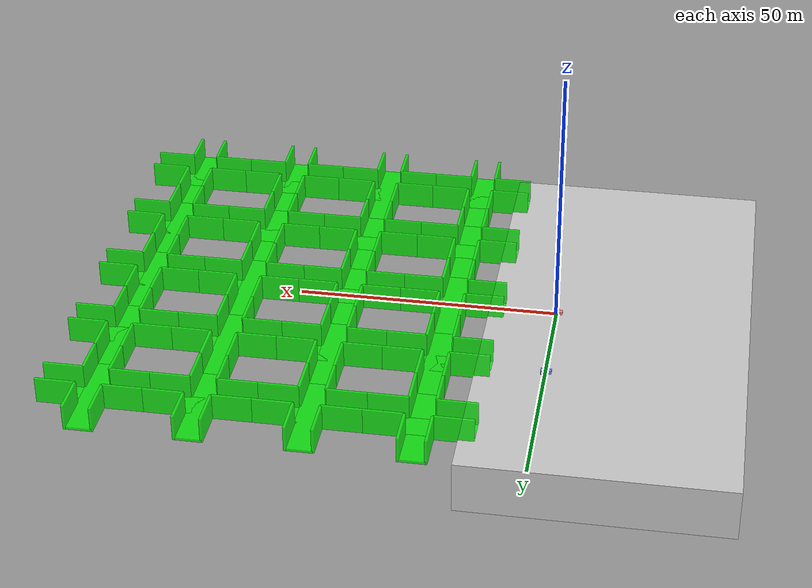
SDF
<sdf version='1.9'>
  <world name='levels'>
    <plugin name='gz::sim::systems::Physics' filename='ignition-gazebo-physics-system'/>
    <plugin name='gz::sim::systems::UserCommands' filename='ignition-gazebo-user-commands-system'/>
    <plugin name='gz::sim::systems::SceneBroadcaster' filename='ignition-gazebo-scene-broadcaster-system'/>
    <scene>
      <ambient>0.8 0.8 0.8 1</ambient>
      <background>0.34 0.39 0.43 1</background>
      <grid>false</grid>
      <origin_visual>false</origin_visual>
      <shadows>true</shadows>
    </scene>
    <plugin name='gz::sim' filename='dummy'>
      <performer name='perf_vehicle_red'>
        <ref>vehicle_red</ref>
        <geometry>
          <box>
            <size>2 2 2</size>
          </box>
        </geometry>
      </performer>
      <performer name='perf_vehicle_blue'>
        <ref>vehicle_blue</ref>
        <geometry>
          <box>
            <size>2 2 2</size>
          </box>
        </geometry>
      </performer>
      <level name='level0'>
        <pose>20 -40 2.5 0 0 0</pose>
        <geometry>
          <box>
            <size>40 40 1000</size>
          </box>
        </geometry>
        <ref>tile_1</ref>
      </level>
      <level name='level1'>
        <pose>20 -20 2.5 0 0 0</pose>
        <geometry>
          <box>
            <size>40 40 1000</size>
          </box>
        </geometry>
        <ref>tile_2</ref>
      </level>
      <level name='level3'>
        <pose>20 20 2.5 0 0 0</pose>
        <geometry>
          <box>
            <size>40 40 1000</size>
          </box>
        </geometry>
        <ref>tile_4</ref>
      </level>
      <level name='level4'>
        <pose>20 40 2.5 0 0 0</pose>
        <geometry>
          <box>
            <size>40 40 1000</size>
          </box>
        </geometry>
        <ref>tile_5</ref>
      </level>
      <level name='level5'>
        <pose>40 -40 2.5 0 0 0</pose>
        <geometry>
          <box>
            <size>40 40 1000</size>
          </box>
        </geometry>
        <ref>tile_6</ref>
      </level>
      <level name='level6'>
        <pose>40 -20 2.5 0 0 0</pose>
        <geometry>
          <box>
            <size>40 40 1000</size>
          </box>
        </geometry>
        <ref>tile_7</ref>
      </level>
      <level name='level7'>
        <pose>40 0 2.5 0 0 0</pose>
        <geometry>
          <box>
            <size>40 40 1000</size>
          </box>
        </geometry>
        <ref>tile_8</ref>
      </level>
      <level name='level8'>
        <pose>40 20 2.5 0 0 0</pose>
        <geometry>
          <box>
            <size>40 40 1000</size>
          </box>
        </geometry>
        <ref>tile_9</ref>
      </level>
      <level name='level9'>
        <pose>40 40 2.5 0 0 0</pose>
        <geometry>
          <box>
            <size>40 40 1000</size>
          </box>
        </geometry>
        <ref>tile_10</ref>
      </level>
      <level name='level10'>
        <pose>60 -40 2.5 0 0 0</pose>
        <geometry>
          <box>
            <size>40 40 1000</size>
          </box>
        </geometry>
        <ref>tile_11</ref>
      </level>
      <level name='level11'>
        <pose>60 -20 2.5 0 0 0</pose>
        <geometry>
          <box>
            <size>40 40 1000</size>
          </box>
        </geometry>
        <ref>tile_12</ref>
      </level>
      <level name='level12'>
        <pose>60 0 2.5 0 0 0</pose>
        <geometry>
          <box>
            <size>40 40 1000</size>
          </box>
        </geometry>
        <ref>tile_13</ref>
      </level>
      <level name='level13'>
        <pose>60 20 2.5 0 0 0</pose>
        <geometry>
          <box>
            <size>40 40 1000</size>
          </box>
        </geometry>
        <ref>tile_14</ref>
      </level>
      <level name='level14'>
        <pose>60 40 2.5 0 0 0</pose>
        <geometry>
          <box>
            <size>40 40 1000</size>
          </box>
        </geometry>
        <ref>tile_15</ref>
      </level>
      <level name='level15'>
        <pose>80 -40 2.5 0 0 0</pose>
        <geometry>
          <box>
            <size>40 40 1000</size>
          </box>
        </geometry>
        <ref>tile_16</ref>
      </level>
      <level name='level16'>
        <pose>80 -20 2.5 0 0 0</pose>
        <geometry>
          <box>
            <size>40 40 1000</size>
          </box>
        </geometry>
        <ref>tile_17</ref>
      </level>
      <level name='level17'>
        <pose>80 0 2.5 0 0 0</pose>
        <geometry>
          <box>
            <size>40 40 1000</size>
          </box>
        </geometry>
        <ref>tile_18</ref>
      </level>
      <level name='level18'>
        <pose>80 20 2.5 0 0 0</pose>
        <geometry>
          <box>
            <size>40 40 1000</size>
          </box>
        </geometry>
        <ref>tile_19</ref>
      </level>
      <level name='level19'>
        <pose>80 40 2.5 0 0 0</pose>
        <geometry>
          <box>
            <size>40 40 1000</size>
          </box>
        </geometry>
        <ref>tile_20</ref>
      </level>
    </plugin>
    <gravity>0 0 -9.8</gravity>
    <magnetic_field>6e-06 2.3e-05 -4.2e-05</magnetic_field>
    <atmosphere type='adiabatic'/>
    <physics type='ode'>
      <max_step_size>0.001</max_step_size>
      <real_time_factor>1</real_time_factor>
      <real_time_update_rate>1000</real_time_update_rate>
    </physics>
    <model name='vehicle_red'>
      <pose>0 0 0.325 0 -0 0</pose>
      <link name='chassis'>
        <pose>-0.151427 0 0.175 0 -0 0</pose>
        <inertial>
          <mass>1.14395</mass>
          <inertia>
            <ixx>0.126164</ixx>
            <ixy>0</ixy>
            <ixz>0</ixz>
            <iyy>0.41651899999999997</iyy>
            <iyz>0</iyz>
            <izz>0.481014</izz>
          </inertia>
          <pose>0 0 0 0 -0 0</pose>
        </inertial>
        <visual name='visual'>
          <geometry>
            <box>
              <size>2.01142 1 0.568726</size>
            </box>
          </geometry>
          <material>
            <ambient>1 0.5 0.5 1</ambient>
            <diffuse>1 0.5 0.5 1</diffuse>
            <specular>1 0.5 0.5 1</specular>
          </material>
        </visual>
        <collision name='collision'>
          <geometry>
            <box>
              <size>2.01142 1 0.568726</size>
            </box>
          </geometry>
          <surface>
            <friction>
              <ode/>
            </friction>
            <bounce/>
            <contact/>
          </surface>
        </collision>
        <enable_wind>false</enable_wind>
      </link>
      <link name='left_wheel'>
        <pose>0.554283 0.625029 -0.025 -1.5707 0 0</pose>
        <inertial>
          <mass>2</mass>
          <inertia>
            <ixx>0.14583299999999999</ixx>
            <ixy>0</ixy>
            <ixz>0</ixz>
            <iyy>0.14583299999999999</iyy>
            <iyz>0</iyz>
            <izz>0.125</izz>
          </inertia>
          <pose>0 0 0 0 -0 0</pose>
        </inertial>
        <visual name='visual'>
          <geometry>
            <sphere>
              <radius>0.29999999999999999</radius>
            </sphere>
          </geometry>
          <material>
            <ambient>0.2 0.2 0.2 1</ambient>
            <diffuse>0.2 0.2 0.2 1</diffuse>
            <specular>0.2 0.2 0.2 1</specular>
          </material>
        </visual>
        <collision name='collision'>
          <geometry>
            <sphere>
              <radius>0.29999999999999999</radius>
            </sphere>
          </geometry>
          <surface>
            <friction>
              <ode/>
            </friction>
            <bounce/>
            <contact/>
          </surface>
        </collision>
        <enable_wind>false</enable_wind>
      </link>
      <link name='right_wheel'>
        <pose>0.554282 -0.625029 -0.025 -1.5707 0 0</pose>
        <inertial>
          <mass>2</mass>
          <inertia>
            <ixx>0.14583299999999999</ixx>
            <ixy>0</ixy>
            <ixz>0</ixz>
            <iyy>0.14583299999999999</iyy>
            <iyz>0</iyz>
            <izz>0.125</izz>
          </inertia>
          <pose>0 0 0 0 -0 0</pose>
        </inertial>
        <visual name='visual'>
          <geometry>
            <sphere>
              <radius>0.29999999999999999</radius>
            </sphere>
          </geometry>
          <material>
            <ambient>0.2 0.2 0.2 1</ambient>
            <diffuse>0.2 0.2 0.2 1</diffuse>
            <specular>0.2 0.2 0.2 1</specular>
          </material>
        </visual>
        <collision name='collision'>
          <geometry>
            <sphere>
              <radius>0.29999999999999999</radius>
            </sphere>
          </geometry>
          <surface>
            <friction>
              <ode/>
            </friction>
            <bounce/>
            <contact/>
          </surface>
        </collision>
        <enable_wind>false</enable_wind>
      </link>
      <link name='caster'>
        <pose>-0.957138 0 -0.125 0 -0 0</pose>
        <inertial>
          <mass>1</mass>
          <inertia>
            <ixx>0.10000000000000001</ixx>
            <ixy>0</ixy>
            <ixz>0</ixz>
            <iyy>0.10000000000000001</iyy>
            <iyz>0</iyz>
            <izz>0.10000000000000001</izz>
          </inertia>
          <pose>0 0 0 0 -0 0</pose>
        </inertial>
        <visual name='visual'>
          <geometry>
            <sphere>
              <radius>0.20000000000000001</radius>
            </sphere>
          </geometry>
          <material>
            <ambient>0.2 0.2 0.2 1</ambient>
            <diffuse>0.2 0.2 0.2 1</diffuse>
            <specular>0.2 0.2 0.2 1</specular>
          </material>
        </visual>
        <collision name='collision'>
          <geometry>
            <sphere>
              <radius>0.20000000000000001</radius>
            </sphere>
          </geometry>
          <surface>
            <friction>
              <ode/>
            </friction>
            <bounce/>
            <contact/>
          </surface>
        </collision>
        <enable_wind>false</enable_wind>
      </link>
      <joint name='left_wheel_joint' type='revolute'>
        <parent>chassis</parent>
        <child>left_wheel</child>
        <axis>
          <xyz>0 0 1</xyz>
          <limit>
            <lower>-1.7976900000000001e+308</lower>
            <upper>1.7976900000000001e+308</upper>
            <effort>inf</effort>
            <velocity>inf</velocity>
            <stiffness>100000000</stiffness>
            <dissipation>1</dissipation>
          </limit>
          <dynamics>
            <spring_reference>0</spring_reference>
            <spring_stiffness>0</spring_stiffness>
            <damping>0</damping>
            <friction>0</friction>
          </dynamics>
        </axis>
        <pose>0 0 0 0 -0 0</pose>
      </joint>
      <joint name='right_wheel_joint' type='revolute'>
        <parent>chassis</parent>
        <child>right_wheel</child>
        <axis>
          <xyz>0 0 1</xyz>
          <limit>
            <lower>-1.7976900000000001e+308</lower>
            <upper>1.7976900000000001e+308</upper>
            <effort>inf</effort>
            <velocity>inf</velocity>
            <stiffness>100000000</stiffness>
            <dissipation>1</dissipation>
          </limit>
          <dynamics>
            <spring_reference>0</spring_reference>
            <spring_stiffness>0</spring_stiffness>
            <damping>0</damping>
            <friction>0</friction>
          </dynamics>
        </axis>
        <pose>-0 0 0 0 -0 0</pose>
      </joint>
      <joint name='caster_wheel' type='ball'>
        <parent>chassis</parent>
        <child>caster</child>
        <pose>0 0 0 0 -0 0</pose>
      </joint>
      <plugin name='gz::sim::systems::DiffDrive' filename='ignition-gazebo-diff-drive-system'>
        <left_joint>left_wheel_joint</left_joint>
        <right_joint>right_wheel_joint</right_joint>
        <wheel_separation>1.25</wheel_separation>
        <wheel_radius>0.3</wheel_radius>
      </plugin>
      <static>false</static>
      <self_collide>false</self_collide>
    </model>
    <model name='vehicle_blue'>
      <pose>0 20 0.325 0 -0 0</pose>
      <link name='chassis'>
        <pose>-0.151427 0 0.175 0 -0 0</pose>
        <inertial>
          <mass>1.14395</mass>
          <inertia>
            <ixx>0.126164</ixx>
            <ixy>0</ixy>
            <ixz>0</ixz>
            <iyy>0.41651899999999997</iyy>
            <iyz>0</iyz>
            <izz>0.481014</izz>
          </inertia>
          <pose>0 0 0 0 -0 0</pose>
        </inertial>
        <visual name='visual'>
          <geometry>
            <box>
              <size>2.01142 1 0.568726</size>
            </box>
          </geometry>
          <material>
            <ambient>0.5 0.5 1 1</ambient>
            <diffuse>0.5 0.5 1 1</diffuse>
            <specular>0.5 0.5 1 1</specular>
          </material>
        </visual>
        <collision name='collision'>
          <geometry>
            <box>
              <size>2.01142 1 0.568726</size>
            </box>
          </geometry>
          <surface>
            <friction>
              <ode/>
            </friction>
            <bounce/>
            <contact/>
          </surface>
        </collision>
        <enable_wind>false</enable_wind>
      </link>
      <link name='left_wheel'>
        <pose>0.554283 0.625029 -0.025 -1.5707 0 0</pose>
        <inertial>
          <mass>2</mass>
          <inertia>
            <ixx>0.14583299999999999</ixx>
            <ixy>0</ixy>
            <ixz>0</ixz>
            <iyy>0.14583299999999999</iyy>
            <iyz>0</iyz>
            <izz>0.125</izz>
          </inertia>
          <pose>0 0 0 0 -0 0</pose>
        </inertial>
        <visual name='visual'>
          <geometry>
            <sphere>
              <radius>0.29999999999999999</radius>
            </sphere>
          </geometry>
          <material>
            <ambient>0.2 0.2 0.2 1</ambient>
            <diffuse>0.2 0.2 0.2 1</diffuse>
            <specular>0.2 0.2 0.2 1</specular>
          </material>
        </visual>
        <collision name='collision'>
          <geometry>
            <sphere>
              <radius>0.29999999999999999</radius>
            </sphere>
          </geometry>
          <surface>
            <friction>
              <ode/>
            </friction>
            <bounce/>
            <contact/>
          </surface>
        </collision>
        <enable_wind>false</enable_wind>
      </link>
      <link name='right_wheel'>
        <pose>0.554282 -0.625029 -0.025 -1.5707 0 0</pose>
        <inertial>
          <mass>2</mass>
          <inertia>
            <ixx>0.14583299999999999</ixx>
            <ixy>0</ixy>
            <ixz>0</ixz>
            <iyy>0.14583299999999999</iyy>
            <iyz>0</iyz>
            <izz>0.125</izz>
          </inertia>
          <pose>0 0 0 0 -0 0</pose>
        </inertial>
        <visual name='visual'>
          <geometry>
            <sphere>
              <radius>0.29999999999999999</radius>
            </sphere>
          </geometry>
          <material>
            <ambient>0.2 0.2 0.2 1</ambient>
            <diffuse>0.2 0.2 0.2 1</diffuse>
            <specular>0.2 0.2 0.2 1</specular>
          </material>
        </visual>
        <collision name='collision'>
          <geometry>
            <sphere>
              <radius>0.29999999999999999</radius>
            </sphere>
          </geometry>
          <surface>
            <friction>
              <ode/>
            </friction>
            <bounce/>
            <contact/>
          </surface>
        </collision>
        <enable_wind>false</enable_wind>
      </link>
      <link name='caster'>
        <pose>-0.957138 0 -0.125 0 -0 0</pose>
        <inertial>
          <mass>1</mass>
          <inertia>
            <ixx>0.10000000000000001</ixx>
            <ixy>0</ixy>
            <ixz>0</ixz>
            <iyy>0.10000000000000001</iyy>
            <iyz>0</iyz>
            <izz>0.10000000000000001</izz>
          </inertia>
          <pose>0 0 0 0 -0 0</pose>
        </inertial>
        <visual name='visual'>
          <geometry>
            <sphere>
              <radius>0.20000000000000001</radius>
            </sphere>
          </geometry>
          <material>
            <ambient>0.2 0.2 0.2 1</ambient>
            <diffuse>0.2 0.2 0.2 1</diffuse>
            <specular>0.2 0.2 0.2 1</specular>
          </material>
        </visual>
        <collision name='collision'>
          <geometry>
            <sphere>
              <radius>0.20000000000000001</radius>
            </sphere>
          </geometry>
          <surface>
            <friction>
              <ode/>
            </friction>
            <bounce/>
            <contact/>
          </surface>
        </collision>
        <enable_wind>false</enable_wind>
      </link>
      <joint name='left_wheel_joint' type='revolute'>
        <parent>chassis</parent>
        <child>left_wheel</child>
        <axis>
          <xyz>0 0 1</xyz>
          <limit>
            <lower>-1.7976900000000001e+308</lower>
            <upper>1.7976900000000001e+308</upper>
            <effort>inf</effort>
            <velocity>inf</velocity>
            <stiffness>100000000</stiffness>
            <dissipation>1</dissipation>
          </limit>
          <dynamics>
            <spring_reference>0</spring_reference>
            <spring_stiffness>0</spring_stiffness>
            <damping>0</damping>
            <friction>0</friction>
          </dynamics>
        </axis>
        <pose>0 0 0 0 -0 0</pose>
      </joint>
      <joint name='right_wheel_joint' type='revolute'>
        <parent>chassis</parent>
        <child>right_wheel</child>
        <axis>
          <xyz>0 0 1</xyz>
          <limit>
            <lower>-1.7976900000000001e+308</lower>
            <upper>1.7976900000000001e+308</upper>
            <effort>inf</effort>
            <velocity>inf</velocity>
            <stiffness>100000000</stiffness>
            <dissipation>1</dissipation>
          </limit>
          <dynamics>
            <spring_reference>0</spring_reference>
            <spring_stiffness>0</spring_stiffness>
            <damping>0</damping>
            <friction>0</friction>
          </dynamics>
        </axis>
        <pose>-0 0 0 0 -0 0</pose>
      </joint>
      <joint name='caster_wheel' type='ball'>
        <parent>chassis</parent>
        <child>caster</child>
        <pose>0 0 0 0 -0 0</pose>
      </joint>
      <plugin name='gz::sim::systems::DiffDrive' filename='ignition-gazebo-diff-drive-system'>
        <left_joint>left_wheel_joint</left_joint>
        <right_joint>right_wheel_joint</right_joint>
        <wheel_separation>1.25</wheel_separation>
        <wheel_radius>0.3</wheel_radius>
      </plugin>
      <static>false</static>
      <self_collide>false</self_collide>
    </model>
    <model name='stage'>
      <pose>-12 0 -5 0 -0 0</pose>
      <static>true</static>
      <link name='link'>
        <collision name='collision'>
          <geometry>
            <box>
              <size>50 100 10</size>
            </box>
          </geometry>
          <surface>
            <friction>
              <ode/>
            </friction>
            <bounce/>
            <contact/>
          </surface>
        </collision>
        <visual name='visual'>
          <geometry>
            <box>
              <size>50 100 10</size>
            </box>
          </geometry>
          <material>
            <ambient>0.8 0.8 0.8 1</ambient>
            <diffuse>0.8 0.8 0.8 1</diffuse>
            <specular>0.8 0.8 0.8 1</specular>
          </material>
        </visual>
        <pose>0 0 0 0 -0 0</pose>
        <inertial>
          <pose>0 0 0 0 -0 0</pose>
          <mass>1</mass>
          <inertia>
            <ixx>1</ixx>
            <ixy>0</ixy>
            <ixz>0</ixz>
            <iyy>1</iyy>
            <iyz>0</iyz>
            <izz>1</izz>
          </inertia>
        </inertial>
        <enable_wind>false</enable_wind>
      </link>
      <self_collide>false</self_collide>
    </model>
    <model name='tile_1'>
      <pose>20 -40 0 0 0 -1.5708</pose>
      <static>true</static>
      <link name='link'>
        <collision name='collision_0'>
          <pose>0 0 -0.25 0 0 0</pose>
          <geometry>
            <box>
              <size>5 20 0.5</size>
            </box>
          </geometry>
          <surface>
            <friction>
              <ode/>
            </friction>
            <bounce/>
            <contact/>
          </surface>
        </collision>
        <visual name='visual_0'>
          <pose>0 0 -0.25 0 0 0</pose>
          <geometry>
            <box>
              <size>5 20 0.5</size>
            </box>
          </geometry>
          <material>
            <ambient>0 1 0 0.8</ambient>
            <diffuse>0 1 0 0.8</diffuse>
            <specular>1 1 1 0.8</specular>
          </material>
        </visual>
        <collision name='collision_1'>
          <pose>0 0 -0.25 0 0 1.57</pose>
          <geometry>
            <box>
              <size>5 20 0.5</size>
            </box>
          </geometry>
          <surface>
            <friction>
              <ode/>
            </friction>
            <bounce/>
            <contact/>
          </surface>
        </collision>
        <visual name='visual_1'>
          <pose>0 0 -0.25 0 0 1.57</pose>
          <geometry>
            <box>
              <size>5 20 0.5</size>
            </box>
          </geometry>
          <material>
            <ambient>0 1 0 0.8</ambient>
            <diffuse>0 1 0 0.8</diffuse>
            <specular>1 1 1 0.8</specular>
          </material>
        </visual>
        <collision name='collision_2'>
          <pose>-2.5 6.25 2 3.14 -1.57 0</pose>
          <geometry>
            <box>
              <size>5 7.5 0.5</size>
            </box>
          </geometry>
          <surface>
            <friction>
              <ode/>
            </friction>
            <bounce/>
            <contact/>
          </surface>
        </collision>
        <visual name='visual_2'>
          <pose>-2.5 6.25 2 3.14 -1.57 0</pose>
          <geometry>
            <box>
              <size>5 7.5 0.5</size>
            </box>
          </geometry>
          <material>
            <ambient>0 1 0 0.8</ambient>
            <diffuse>0 1 0 0.8</diffuse>
            <specular>1 1 1 0.8</specular>
          </material>
        </visual>
        <collision name='collision_3'>
          <pose>2.5 6.25 2 3.14 -1.57 0</pose>
          <geometry>
            <box>
              <size>5 7.5 0.5</size>
            </box>
          </geometry>
          <surface>
            <friction>
              <ode/>
            </friction>
            <bounce/>
            <contact/>
          </surface>
        </collision>
        <visual name='visual_3'>
          <pose>2.5 6.25 2 3.14 -1.57 0</pose>
          <geometry>
            <box>
              <size>5 7.5 0.5</size>
            </box>
          </geometry>
          <material>
            <ambient>0 1 0 0.8</ambient>
            <diffuse>0 1 0 0.8</diffuse>
            <specular>1 1 1 0.8</specular>
          </material>
        </visual>
        <collision name='collision_4'>
          <pose>-2.5 -6.25 2 3.14 -1.57 0</pose>
          <geometry>
            <box>
              <size>5 7.5 0.5</size>
            </box>
          </geometry>
          <surface>
            <friction>
              <ode/>
            </friction>
            <bounce/>
            <contact/>
          </surface>
        </collision>
        <visual name='visual_4'>
          <pose>-2.5 -6.25 2 3.14 -1.57 0</pose>
          <geometry>
            <box>
              <size>5 7.5 0.5</size>
            </box>
          </geometry>
          <material>
            <ambient>0 1 0 0.8</ambient>
            <diffuse>0 1 0 0.8</diffuse>
            <specular>1 1 1 0.8</specular>
          </material>
        </visual>
        <collision name='collision_5'>
          <pose>2.5 -6.25 2 3.14 -1.57 0</pose>
          <geometry>
            <box>
              <size>5 7.5 0.5</size>
            </box>
          </geometry>
          <surface>
            <friction>
              <ode/>
            </friction>
            <bounce/>
            <contact/>
          </surface>
        </collision>
        <visual name='visual_5'>
          <pose>2.5 -6.25 2 3.14 -1.57 0</pose>
          <geometry>
            <box>
              <size>5 7.5 0.5</size>
            </box>
          </geometry>
          <material>
            <ambient>0 1 0 0.8</ambient>
            <diffuse>0 1 0 0.8</diffuse>
            <specular>1 1 1 0.8</specular>
          </material>
        </visual>
        <collision name='collision_6'>
          <pose>6.25 2.5 2 1.57 1.57 0</pose>
          <geometry>
            <box>
              <size>5 7.5 0.5</size>
            </box>
          </geometry>
          <surface>
            <friction>
              <ode/>
            </friction>
            <bounce/>
            <contact/>
          </surface>
        </collision>
        <visual name='visual_6'>
          <pose>6.25 2.5 2 1.57 1.57 0</pose>
          <geometry>
            <box>
              <size>5 7.5 0.5</size>
            </box>
          </geometry>
          <material>
            <ambient>0 1 0 0.8</ambient>
            <diffuse>0 1 0 0.8</diffuse>
            <specular>1 1 1 0.8</specular>
          </material>
        </visual>
        <collision name='collision_7'>
          <pose>-6.25 2.5 2 1.57 1.57 0</pose>
          <geometry>
            <box>
              <size>5 7.5 0.5</size>
            </box>
          </geometry>
          <surface>
            <friction>
              <ode/>
            </friction>
            <bounce/>
            <contact/>
          </surface>
        </collision>
        <visual name='visual_7'>
          <pose>-6.25 2.5 2 1.57 1.57 0</pose>
          <geometry>
            <box>
              <size>5 7.5 0.5</size>
            </box>
          </geometry>
          <material>
            <ambient>0 1 0 0.8</ambient>
            <diffuse>0 1 0 0.8</diffuse>
            <specular>1 1 1 0.8</specular>
          </material>
        </visual>
        <collision name='collision_8'>
          <pose>6.25 -2.5 2 1.57 1.57 0</pose>
          <geometry>
            <box>
              <size>5 7.5 0.5</size>
            </box>
          </geometry>
          <surface>
            <friction>
              <ode/>
            </friction>
            <bounce/>
            <contact/>
          </surface>
        </collision>
        <visual name='visual_8'>
          <pose>6.25 -2.5 2 1.57 1.57 0</pose>
          <geometry>
            <box>
              <size>5 7.5 0.5</size>
            </box>
          </geometry>
          <material>
            <ambient>0 1 0 0.8</ambient>
            <diffuse>0 1 0 0.8</diffuse>
            <specular>1 1 1 0.8</specular>
          </material>
        </visual>
        <collision name='collision_9'>
          <pose>-6.25 -2.5 2 1.57 1.57 0</pose>
          <geometry>
            <box>
              <size>5 7.5 0.5</size>
            </box>
          </geometry>
          <surface>
            <friction>
              <ode/>
            </friction>
            <bounce/>
            <contact/>
          </surface>
        </collision>
        <visual name='visual_9'>
          <pose>-6.25 -2.5 2 1.57 1.57 0</pose>
          <geometry>
            <box>
              <size>5 7.5 0.5</size>
            </box>
          </geometry>
          <material>
            <ambient>0 1 0 0.8</ambient>
            <diffuse>0 1 0 0.8</diffuse>
            <specular>1 1 1 0.8</specular>
          </material>
        </visual>
        <pose>0 0 0 0 -0 0</pose>
        <inertial>
          <pose>0 0 0 0 -0 0</pose>
          <mass>1</mass>
          <inertia>
            <ixx>1</ixx>
            <ixy>0</ixy>
            <ixz>0</ixz>
            <iyy>1</iyy>
            <iyz>0</iyz>
            <izz>1</izz>
          </inertia>
        </inertial>
        <enable_wind>false</enable_wind>
      </link>
      <self_collide>false</self_collide>
    </model>
    <model name='tile_2'>
      <pose>20 -20 0 0 0 -1.5708</pose>
      <static>true</static>
      <link name='link'>
        <collision name='collision_0'>
          <pose>0 0 -0.25 0 0 0</pose>
          <geometry>
            <box>
              <size>5 20 0.5</size>
            </box>
          </geometry>
          <surface>
            <friction>
              <ode/>
            </friction>
            <bounce/>
            <contact/>
          </surface>
        </collision>
        <visual name='visual_0'>
          <pose>0 0 -0.25 0 0 0</pose>
          <geometry>
            <box>
              <size>5 20 0.5</size>
            </box>
          </geometry>
          <material>
            <ambient>0 1 0 0.8</ambient>
            <diffuse>0 1 0 0.8</diffuse>
            <specular>1 1 1 0.8</specular>
          </material>
        </visual>
        <collision name='collision_1'>
          <pose>0 0 -0.25 0 0 1.57</pose>
          <geometry>
            <box>
              <size>5 20 0.5</size>
            </box>
          </geometry>
          <surface>
            <friction>
              <ode/>
            </friction>
            <bounce/>
            <contact/>
          </surface>
        </collision>
        <visual name='visual_1'>
          <pose>0 0 -0.25 0 0 1.57</pose>
          <geometry>
            <box>
              <size>5 20 0.5</size>
            </box>
          </geometry>
          <material>
            <ambient>0 1 0 0.8</ambient>
            <diffuse>0 1 0 0.8</diffuse>
            <specular>1 1 1 0.8</specular>
          </material>
        </visual>
        <collision name='collision_2'>
          <pose>-2.5 6.25 2 3.14 -1.57 0</pose>
          <geometry>
            <box>
              <size>5 7.5 0.5</size>
            </box>
          </geometry>
          <surface>
            <friction>
              <ode/>
            </friction>
            <bounce/>
            <contact/>
          </surface>
        </collision>
        <visual name='visual_2'>
          <pose>-2.5 6.25 2 3.14 -1.57 0</pose>
          <geometry>
            <box>
              <size>5 7.5 0.5</size>
            </box>
          </geometry>
          <material>
            <ambient>0 1 0 0.8</ambient>
            <diffuse>0 1 0 0.8</diffuse>
            <specular>1 1 1 0.8</specular>
          </material>
        </visual>
        <collision name='collision_3'>
          <pose>2.5 6.25 2 3.14 -1.57 0</pose>
          <geometry>
            <box>
              <size>5 7.5 0.5</size>
            </box>
          </geometry>
          <surface>
            <friction>
              <ode/>
            </friction>
            <bounce/>
            <contact/>
          </surface>
        </collision>
        <visual name='visual_3'>
          <pose>2.5 6.25 2 3.14 -1.57 0</pose>
          <geometry>
            <box>
              <size>5 7.5 0.5</size>
            </box>
          </geometry>
          <material>
            <ambient>0 1 0 0.8</ambient>
            <diffuse>0 1 0 0.8</diffuse>
            <specular>1 1 1 0.8</specular>
          </material>
        </visual>
        <collision name='collision_4'>
          <pose>-2.5 -6.25 2 3.14 -1.57 0</pose>
          <geometry>
            <box>
              <size>5 7.5 0.5</size>
            </box>
          </geometry>
          <surface>
            <friction>
              <ode/>
            </friction>
            <bounce/>
            <contact/>
          </surface>
        </collision>
        <visual name='visual_4'>
          <pose>-2.5 -6.25 2 3.14 -1.57 0</pose>
          <geometry>
            <box>
              <size>5 7.5 0.5</size>
            </box>
          </geometry>
          <material>
            <ambient>0 1 0 0.8</ambient>
            <diffuse>0 1 0 0.8</diffuse>
            <specular>1 1 1 0.8</specular>
          </material>
        </visual>
        <collision name='collision_5'>
          <pose>2.5 -6.25 2 3.14 -1.57 0</pose>
          <geometry>
            <box>
              <size>5 7.5 0.5</size>
            </box>
          </geometry>
          <surface>
            <friction>
              <ode/>
            </friction>
            <bounce/>
            <contact/>
          </surface>
        </collision>
        <visual name='visual_5'>
          <pose>2.5 -6.25 2 3.14 -1.57 0</pose>
          <geometry>
            <box>
              <size>5 7.5 0.5</size>
            </box>
          </geometry>
          <material>
            <ambient>0 1 0 0.8</ambient>
            <diffuse>0 1 0 0.8</diffuse>
            <specular>1 1 1 0.8</specular>
          </material>
        </visual>
        <collision name='collision_6'>
          <pose>6.25 2.5 2 1.57 1.57 0</pose>
          <geometry>
            <box>
              <size>5 7.5 0.5</size>
            </box>
          </geometry>
          <surface>
            <friction>
              <ode/>
            </friction>
            <bounce/>
            <contact/>
          </surface>
        </collision>
        <visual name='visual_6'>
          <pose>6.25 2.5 2 1.57 1.57 0</pose>
          <geometry>
            <box>
              <size>5 7.5 0.5</size>
            </box>
          </geometry>
          <material>
            <ambient>0 1 0 0.8</ambient>
            <diffuse>0 1 0 0.8</diffuse>
            <specular>1 1 1 0.8</specular>
          </material>
        </visual>
        <collision name='collision_7'>
          <pose>-6.25 2.5 2 1.57 1.57 0</pose>
          <geometry>
            <box>
              <size>5 7.5 0.5</size>
            </box>
          </geometry>
          <surface>
            <friction>
              <ode/>
            </friction>
            <bounce/>
            <contact/>
          </surface>
        </collision>
        <visual name='visual_7'>
          <pose>-6.25 2.5 2 1.57 1.57 0</pose>
          <geometry>
            <box>
              <size>5 7.5 0.5</size>
            </box>
          </geometry>
          <material>
            <ambient>0 1 0 0.8</ambient>
            <diffuse>0 1 0 0.8</diffuse>
            <specular>1 1 1 0.8</specular>
          </material>
        </visual>
        <collision name='collision_8'>
          <pose>6.25 -2.5 2 1.57 1.57 0</pose>
          <geometry>
            <box>
              <size>5 7.5 0.5</size>
            </box>
          </geometry>
          <surface>
            <friction>
              <ode/>
            </friction>
            <bounce/>
            <contact/>
          </surface>
        </collision>
        <visual name='visual_8'>
          <pose>6.25 -2.5 2 1.57 1.57 0</pose>
          <geometry>
            <box>
              <size>5 7.5 0.5</size>
            </box>
          </geometry>
          <material>
            <ambient>0 1 0 0.8</ambient>
            <diffuse>0 1 0 0.8</diffuse>
            <specular>1 1 1 0.8</specular>
          </material>
        </visual>
        <collision name='collision_9'>
          <pose>-6.25 -2.5 2 1.57 1.57 0</pose>
          <geometry>
            <box>
              <size>5 7.5 0.5</size>
            </box>
          </geometry>
          <surface>
            <friction>
              <ode/>
            </friction>
            <bounce/>
            <contact/>
          </surface>
        </collision>
        <visual name='visual_9'>
          <pose>-6.25 -2.5 2 1.57 1.57 0</pose>
          <geometry>
            <box>
              <size>5 7.5 0.5</size>
            </box>
          </geometry>
          <material>
            <ambient>0 1 0 0.8</ambient>
            <diffuse>0 1 0 0.8</diffuse>
            <specular>1 1 1 0.8</specular>
          </material>
        </visual>
        <pose>0 0 0 0 -0 0</pose>
        <inertial>
          <pose>0 0 0 0 -0 0</pose>
          <mass>1</mass>
          <inertia>
            <ixx>1</ixx>
            <ixy>0</ixy>
            <ixz>0</ixz>
            <iyy>1</iyy>
            <iyz>0</iyz>
            <izz>1</izz>
          </inertia>
        </inertial>
        <enable_wind>false</enable_wind>
      </link>
      <self_collide>false</self_collide>
    </model>
    <model name='tile_3'>
      <pose>20 0 0 0 -0 0</pose>
      <static>true</static>
      <link name='link'>
        <collision name='collision_0'>
          <pose>0 0 -0.25 0 0 0</pose>
          <geometry>
            <box>
              <size>5 20 0.5</size>
            </box>
          </geometry>
          <surface>
            <friction>
              <ode/>
            </friction>
            <bounce/>
            <contact/>
          </surface>
        </collision>
        <visual name='visual_0'>
          <pose>0 0 -0.25 0 0 0</pose>
          <geometry>
            <box>
              <size>5 20 0.5</size>
            </box>
          </geometry>
          <material>
            <ambient>0 1 0 0.8</ambient>
            <diffuse>0 1 0 0.8</diffuse>
            <specular>1 1 1 0.8</specular>
          </material>
        </visual>
        <collision name='collision_1'>
          <pose>0 0 -0.25 0 0 1.57</pose>
          <geometry>
            <box>
              <size>5 20 0.5</size>
            </box>
          </geometry>
          <surface>
            <friction>
              <ode/>
            </friction>
            <bounce/>
            <contact/>
          </surface>
        </collision>
        <visual name='visual_1'>
          <pose>0 0 -0.25 0 0 1.57</pose>
          <geometry>
            <box>
              <size>5 20 0.5</size>
            </box>
          </geometry>
          <material>
            <ambient>0 1 0 0.8</ambient>
            <diffuse>0 1 0 0.8</diffuse>
            <specular>1 1 1 0.8</specular>
          </material>
        </visual>
        <collision name='collision_2'>
          <pose>-2.5 6.25 2 3.14 -1.57 0</pose>
          <geometry>
            <box>
              <size>5 7.5 0.5</size>
            </box>
          </geometry>
          <surface>
            <friction>
              <ode/>
            </friction>
            <bounce/>
            <contact/>
          </surface>
        </collision>
        <visual name='visual_2'>
          <pose>-2.5 6.25 2 3.14 -1.57 0</pose>
          <geometry>
            <box>
              <size>5 7.5 0.5</size>
            </box>
          </geometry>
          <material>
            <ambient>0 1 0 0.8</ambient>
            <diffuse>0 1 0 0.8</diffuse>
            <specular>1 1 1 0.8</specular>
          </material>
        </visual>
        <collision name='collision_3'>
          <pose>2.5 6.25 2 3.14 -1.57 0</pose>
          <geometry>
            <box>
              <size>5 7.5 0.5</size>
            </box>
          </geometry>
          <surface>
            <friction>
              <ode/>
            </friction>
            <bounce/>
            <contact/>
          </surface>
        </collision>
        <visual name='visual_3'>
          <pose>2.5 6.25 2 3.14 -1.57 0</pose>
          <geometry>
            <box>
              <size>5 7.5 0.5</size>
            </box>
          </geometry>
          <material>
            <ambient>0 1 0 0.8</ambient>
            <diffuse>0 1 0 0.8</diffuse>
            <specular>1 1 1 0.8</specular>
          </material>
        </visual>
        <collision name='collision_4'>
          <pose>-2.5 -6.25 2 3.14 -1.57 0</pose>
          <geometry>
            <box>
              <size>5 7.5 0.5</size>
            </box>
          </geometry>
          <surface>
            <friction>
              <ode/>
            </friction>
            <bounce/>
            <contact/>
          </surface>
        </collision>
        <visual name='visual_4'>
          <pose>-2.5 -6.25 2 3.14 -1.57 0</pose>
          <geometry>
            <box>
              <size>5 7.5 0.5</size>
            </box>
          </geometry>
          <material>
            <ambient>0 1 0 0.8</ambient>
            <diffuse>0 1 0 0.8</diffuse>
            <specular>1 1 1 0.8</specular>
          </material>
        </visual>
        <collision name='collision_5'>
          <pose>2.5 -6.25 2 3.14 -1.57 0</pose>
          <geometry>
            <box>
              <size>5 7.5 0.5</size>
            </box>
          </geometry>
          <surface>
            <friction>
              <ode/>
            </friction>
            <bounce/>
            <contact/>
          </surface>
        </collision>
        <visual name='visual_5'>
          <pose>2.5 -6.25 2 3.14 -1.57 0</pose>
          <geometry>
            <box>
              <size>5 7.5 0.5</size>
            </box>
          </geometry>
          <material>
            <ambient>0 1 0 0.8</ambient>
            <diffuse>0 1 0 0.8</diffuse>
            <specular>1 1 1 0.8</specular>
          </material>
        </visual>
        <collision name='collision_6'>
          <pose>6.25 2.5 2 1.57 1.57 0</pose>
          <geometry>
            <box>
              <size>5 7.5 0.5</size>
            </box>
          </geometry>
          <surface>
            <friction>
              <ode/>
            </friction>
            <bounce/>
            <contact/>
          </surface>
        </collision>
        <visual name='visual_6'>
          <pose>6.25 2.5 2 1.57 1.57 0</pose>
          <geometry>
            <box>
              <size>5 7.5 0.5</size>
            </box>
          </geometry>
          <material>
            <ambient>0 1 0 0.8</ambient>
            <diffuse>0 1 0 0.8</diffuse>
            <specular>1 1 1 0.8</specular>
          </material>
        </visual>
        <collision name='collision_7'>
          <pose>-6.25 2.5 2 1.57 1.57 0</pose>
          <geometry>
            <box>
              <size>5 7.5 0.5</size>
            </box>
          </geometry>
          <surface>
            <friction>
              <ode/>
            </friction>
            <bounce/>
            <contact/>
          </surface>
        </collision>
        <visual name='visual_7'>
          <pose>-6.25 2.5 2 1.57 1.57 0</pose>
          <geometry>
            <box>
              <size>5 7.5 0.5</size>
            </box>
          </geometry>
          <material>
            <ambient>0 1 0 0.8</ambient>
            <diffuse>0 1 0 0.8</diffuse>
            <specular>1 1 1 0.8</specular>
          </material>
        </visual>
        <collision name='collision_8'>
          <pose>6.25 -2.5 2 1.57 1.57 0</pose>
          <geometry>
            <box>
              <size>5 7.5 0.5</size>
            </box>
          </geometry>
          <surface>
            <friction>
              <ode/>
            </friction>
            <bounce/>
            <contact/>
          </surface>
        </collision>
        <visual name='visual_8'>
          <pose>6.25 -2.5 2 1.57 1.57 0</pose>
          <geometry>
            <box>
              <size>5 7.5 0.5</size>
            </box>
          </geometry>
          <material>
            <ambient>0 1 0 0.8</ambient>
            <diffuse>0 1 0 0.8</diffuse>
            <specular>1 1 1 0.8</specular>
          </material>
        </visual>
        <collision name='collision_9'>
          <pose>-6.25 -2.5 2 1.57 1.57 0</pose>
          <geometry>
            <box>
              <size>5 7.5 0.5</size>
            </box>
          </geometry>
          <surface>
            <friction>
              <ode/>
            </friction>
            <bounce/>
            <contact/>
          </surface>
        </collision>
        <visual name='visual_9'>
          <pose>-6.25 -2.5 2 1.57 1.57 0</pose>
          <geometry>
            <box>
              <size>5 7.5 0.5</size>
            </box>
          </geometry>
          <material>
            <ambient>0 1 0 0.8</ambient>
            <diffuse>0 1 0 0.8</diffuse>
            <specular>1 1 1 0.8</specular>
          </material>
        </visual>
        <pose>0 0 0 0 -0 0</pose>
        <inertial>
          <pose>0 0 0 0 -0 0</pose>
          <mass>1</mass>
          <inertia>
            <ixx>1</ixx>
            <ixy>0</ixy>
            <ixz>0</ixz>
            <iyy>1</iyy>
            <iyz>0</iyz>
            <izz>1</izz>
          </inertia>
        </inertial>
        <enable_wind>false</enable_wind>
      </link>
      <self_collide>false</self_collide>
    </model>
    <model name='tile_4'>
      <pose>20 20 0 0 -0 0</pose>
      <static>true</static>
      <link name='link'>
        <collision name='collision_0'>
          <pose>0 0 -0.25 0 0 0</pose>
          <geometry>
            <box>
              <size>5 20 0.5</size>
            </box>
          </geometry>
          <surface>
            <friction>
              <ode/>
            </friction>
            <bounce/>
            <contact/>
          </surface>
        </collision>
        <visual name='visual_0'>
          <pose>0 0 -0.25 0 0 0</pose>
          <geometry>
            <box>
              <size>5 20 0.5</size>
            </box>
          </geometry>
          <material>
            <ambient>0 1 0 0.8</ambient>
            <diffuse>0 1 0 0.8</diffuse>
            <specular>1 1 1 0.8</specular>
          </material>
        </visual>
        <collision name='collision_1'>
          <pose>0 0 -0.25 0 0 1.57</pose>
          <geometry>
            <box>
              <size>5 20 0.5</size>
            </box>
          </geometry>
          <surface>
            <friction>
              <ode/>
            </friction>
            <bounce/>
            <contact/>
          </surface>
        </collision>
        <visual name='visual_1'>
          <pose>0 0 -0.25 0 0 1.57</pose>
          <geometry>
            <box>
              <size>5 20 0.5</size>
            </box>
          </geometry>
          <material>
            <ambient>0 1 0 0.8</ambient>
            <diffuse>0 1 0 0.8</diffuse>
            <specular>1 1 1 0.8</specular>
          </material>
        </visual>
        <collision name='collision_2'>
          <pose>-2.5 6.25 2 3.14 -1.57 0</pose>
          <geometry>
            <box>
              <size>5 7.5 0.5</size>
            </box>
          </geometry>
          <surface>
            <friction>
              <ode/>
            </friction>
            <bounce/>
            <contact/>
          </surface>
        </collision>
        <visual name='visual_2'>
          <pose>-2.5 6.25 2 3.14 -1.57 0</pose>
          <geometry>
            <box>
              <size>5 7.5 0.5</size>
            </box>
          </geometry>
          <material>
            <ambient>0 1 0 0.8</ambient>
            <diffuse>0 1 0 0.8</diffuse>
            <specular>1 1 1 0.8</specular>
          </material>
        </visual>
        <collision name='collision_3'>
          <pose>2.5 6.25 2 3.14 -1.57 0</pose>
          <geometry>
            <box>
              <size>5 7.5 0.5</size>
            </box>
          </geometry>
          <surface>
            <friction>
              <ode/>
            </friction>
            <bounce/>
            <contact/>
          </surface>
        </collision>
        <visual name='visual_3'>
          <pose>2.5 6.25 2 3.14 -1.57 0</pose>
          <geometry>
            <box>
              <size>5 7.5 0.5</size>
            </box>
          </geometry>
          <material>
            <ambient>0 1 0 0.8</ambient>
            <diffuse>0 1 0 0.8</diffuse>
            <specular>1 1 1 0.8</specular>
          </material>
        </visual>
        <collision name='collision_4'>
          <pose>-2.5 -6.25 2 3.14 -1.57 0</pose>
          <geometry>
            <box>
              <size>5 7.5 0.5</size>
            </box>
          </geometry>
          <surface>
            <friction>
              <ode/>
            </friction>
            <bounce/>
            <contact/>
          </surface>
        </collision>
        <visual name='visual_4'>
          <pose>-2.5 -6.25 2 3.14 -1.57 0</pose>
          <geometry>
            <box>
              <size>5 7.5 0.5</size>
            </box>
          </geometry>
          <material>
            <ambient>0 1 0 0.8</ambient>
            <diffuse>0 1 0 0.8</diffuse>
            <specular>1 1 1 0.8</specular>
          </material>
        </visual>
        <collision name='collision_5'>
          <pose>2.5 -6.25 2 3.14 -1.57 0</pose>
          <geometry>
            <box>
              <size>5 7.5 0.5</size>
            </box>
          </geometry>
          <surface>
            <friction>
              <ode/>
            </friction>
            <bounce/>
            <contact/>
          </surface>
        </collision>
        <visual name='visual_5'>
          <pose>2.5 -6.25 2 3.14 -1.57 0</pose>
          <geometry>
            <box>
              <size>5 7.5 0.5</size>
            </box>
          </geometry>
          <material>
            <ambient>0 1 0 0.8</ambient>
            <diffuse>0 1 0 0.8</diffuse>
            <specular>1 1 1 0.8</specular>
          </material>
        </visual>
        <collision name='collision_6'>
          <pose>6.25 2.5 2 1.57 1.57 0</pose>
          <geometry>
            <box>
              <size>5 7.5 0.5</size>
            </box>
          </geometry>
          <surface>
            <friction>
              <ode/>
            </friction>
            <bounce/>
            <contact/>
          </surface>
        </collision>
        <visual name='visual_6'>
          <pose>6.25 2.5 2 1.57 1.57 0</pose>
          <geometry>
            <box>
              <size>5 7.5 0.5</size>
            </box>
          </geometry>
          <material>
            <ambient>0 1 0 0.8</ambient>
            <diffuse>0 1 0 0.8</diffuse>
            <specular>1 1 1 0.8</specular>
          </material>
        </visual>
        <collision name='collision_7'>
          <pose>-6.25 2.5 2 1.57 1.57 0</pose>
          <geometry>
            <box>
              <size>5 7.5 0.5</size>
            </box>
          </geometry>
          <surface>
            <friction>
              <ode/>
            </friction>
            <bounce/>
            <contact/>
          </surface>
        </collision>
        <visual name='visual_7'>
          <pose>-6.25 2.5 2 1.57 1.57 0</pose>
          <geometry>
            <box>
              <size>5 7.5 0.5</size>
            </box>
          </geometry>
          <material>
            <ambient>0 1 0 0.8</ambient>
            <diffuse>0 1 0 0.8</diffuse>
            <specular>1 1 1 0.8</specular>
          </material>
        </visual>
        <collision name='collision_8'>
          <pose>6.25 -2.5 2 1.57 1.57 0</pose>
          <geometry>
            <box>
              <size>5 7.5 0.5</size>
            </box>
          </geometry>
          <surface>
            <friction>
              <ode/>
            </friction>
            <bounce/>
            <contact/>
          </surface>
        </collision>
        <visual name='visual_8'>
          <pose>6.25 -2.5 2 1.57 1.57 0</pose>
          <geometry>
            <box>
              <size>5 7.5 0.5</size>
            </box>
          </geometry>
          <material>
            <ambient>0 1 0 0.8</ambient>
            <diffuse>0 1 0 0.8</diffuse>
            <specular>1 1 1 0.8</specular>
          </material>
        </visual>
        <collision name='collision_9'>
          <pose>-6.25 -2.5 2 1.57 1.57 0</pose>
          <geometry>
            <box>
              <size>5 7.5 0.5</size>
            </box>
          </geometry>
          <surface>
            <friction>
              <ode/>
            </friction>
            <bounce/>
            <contact/>
          </surface>
        </collision>
        <visual name='visual_9'>
          <pose>-6.25 -2.5 2 1.57 1.57 0</pose>
          <geometry>
            <box>
              <size>5 7.5 0.5</size>
            </box>
          </geometry>
          <material>
            <ambient>0 1 0 0.8</ambient>
            <diffuse>0 1 0 0.8</diffuse>
            <specular>1 1 1 0.8</specular>
          </material>
        </visual>
        <pose>0 0 0 0 -0 0</pose>
        <inertial>
          <pose>0 0 0 0 -0 0</pose>
          <mass>1</mass>
          <inertia>
            <ixx>1</ixx>
            <ixy>0</ixy>
            <ixz>0</ixz>
            <iyy>1</iyy>
            <iyz>0</iyz>
            <izz>1</izz>
          </inertia>
        </inertial>
        <enable_wind>false</enable_wind>
      </link>
      <self_collide>false</self_collide>
    </model>
    <model name='tile_5'>
      <pose>20 40 0 0 0 -1.5708</pose>
      <static>true</static>
      <link name='link'>
        <collision name='collision_0'>
          <pose>0 0 -0.25 0 0 0</pose>
          <geometry>
            <box>
              <size>5 20 0.5</size>
            </box>
          </geometry>
          <surface>
            <friction>
              <ode/>
            </friction>
            <bounce/>
            <contact/>
          </surface>
        </collision>
        <visual name='visual_0'>
          <pose>0 0 -0.25 0 0 0</pose>
          <geometry>
            <box>
              <size>5 20 0.5</size>
            </box>
          </geometry>
          <material>
            <ambient>0 1 0 0.8</ambient>
            <diffuse>0 1 0 0.8</diffuse>
            <specular>1 1 1 0.8</specular>
          </material>
        </visual>
        <collision name='collision_1'>
          <pose>0 0 -0.25 0 0 1.57</pose>
          <geometry>
            <box>
              <size>5 20 0.5</size>
            </box>
          </geometry>
          <surface>
            <friction>
              <ode/>
            </friction>
            <bounce/>
            <contact/>
          </surface>
        </collision>
        <visual name='visual_1'>
          <pose>0 0 -0.25 0 0 1.57</pose>
          <geometry>
            <box>
              <size>5 20 0.5</size>
            </box>
          </geometry>
          <material>
            <ambient>0 1 0 0.8</ambient>
            <diffuse>0 1 0 0.8</diffuse>
            <specular>1 1 1 0.8</specular>
          </material>
        </visual>
        <collision name='collision_2'>
          <pose>-2.5 6.25 2 3.14 -1.57 0</pose>
          <geometry>
            <box>
              <size>5 7.5 0.5</size>
            </box>
          </geometry>
          <surface>
            <friction>
              <ode/>
            </friction>
            <bounce/>
            <contact/>
          </surface>
        </collision>
        <visual name='visual_2'>
          <pose>-2.5 6.25 2 3.14 -1.57 0</pose>
          <geometry>
            <box>
              <size>5 7.5 0.5</size>
            </box>
          </geometry>
          <material>
            <ambient>0 1 0 0.8</ambient>
            <diffuse>0 1 0 0.8</diffuse>
            <specular>1 1 1 0.8</specular>
          </material>
        </visual>
        <collision name='collision_3'>
          <pose>2.5 6.25 2 3.14 -1.57 0</pose>
          <geometry>
            <box>
              <size>5 7.5 0.5</size>
            </box>
          </geometry>
          <surface>
            <friction>
              <ode/>
            </friction>
            <bounce/>
            <contact/>
          </surface>
        </collision>
        <visual name='visual_3'>
          <pose>2.5 6.25 2 3.14 -1.57 0</pose>
          <geometry>
            <box>
              <size>5 7.5 0.5</size>
            </box>
          </geometry>
          <material>
            <ambient>0 1 0 0.8</ambient>
            <diffuse>0 1 0 0.8</diffuse>
            <specular>1 1 1 0.8</specular>
          </material>
        </visual>
        <collision name='collision_4'>
          <pose>-2.5 -6.25 2 3.14 -1.57 0</pose>
          <geometry>
            <box>
              <size>5 7.5 0.5</size>
            </box>
          </geometry>
          <surface>
            <friction>
              <ode/>
            </friction>
            <bounce/>
            <contact/>
          </surface>
        </collision>
        <visual name='visual_4'>
          <pose>-2.5 -6.25 2 3.14 -1.57 0</pose>
          <geometry>
            <box>
              <size>5 7.5 0.5</size>
            </box>
          </geometry>
          <material>
            <ambient>0 1 0 0.8</ambient>
            <diffuse>0 1 0 0.8</diffuse>
            <specular>1 1 1 0.8</specular>
          </material>
        </visual>
        <collision name='collision_5'>
          <pose>2.5 -6.25 2 3.14 -1.57 0</pose>
          <geometry>
            <box>
              <size>5 7.5 0.5</size>
            </box>
          </geometry>
          <surface>
            <friction>
              <ode/>
            </friction>
            <bounce/>
            <contact/>
          </surface>
        </collision>
        <visual name='visual_5'>
          <pose>2.5 -6.25 2 3.14 -1.57 0</pose>
          <geometry>
            <box>
              <size>5 7.5 0.5</size>
            </box>
          </geometry>
          <material>
            <ambient>0 1 0 0.8</ambient>
            <diffuse>0 1 0 0.8</diffuse>
            <specular>1 1 1 0.8</specular>
          </material>
        </visual>
        <collision name='collision_6'>
          <pose>6.25 2.5 2 1.57 1.57 0</pose>
          <geometry>
            <box>
              <size>5 7.5 0.5</size>
            </box>
          </geometry>
          <surface>
            <friction>
              <ode/>
            </friction>
            <bounce/>
            <contact/>
          </surface>
        </collision>
        <visual name='visual_6'>
          <pose>6.25 2.5 2 1.57 1.57 0</pose>
          <geometry>
            <box>
              <size>5 7.5 0.5</size>
            </box>
          </geometry>
          <material>
            <ambient>0 1 0 0.8</ambient>
            <diffuse>0 1 0 0.8</diffuse>
            <specular>1 1 1 0.8</specular>
          </material>
        </visual>
        <collision name='collision_7'>
          <pose>-6.25 2.5 2 1.57 1.57 0</pose>
          <geometry>
            <box>
              <size>5 7.5 0.5</size>
            </box>
          </geometry>
          <surface>
            <friction>
              <ode/>
            </friction>
            <bounce/>
            <contact/>
          </surface>
        </collision>
        <visual name='visual_7'>
          <pose>-6.25 2.5 2 1.57 1.57 0</pose>
          <geometry>
            <box>
              <size>5 7.5 0.5</size>
            </box>
          </geometry>
          <material>
            <ambient>0 1 0 0.8</ambient>
            <diffuse>0 1 0 0.8</diffuse>
            <specular>1 1 1 0.8</specular>
          </material>
        </visual>
        <collision name='collision_8'>
          <pose>6.25 -2.5 2 1.57 1.57 0</pose>
          <geometry>
            <box>
              <size>5 7.5 0.5</size>
            </box>
          </geometry>
          <surface>
            <friction>
              <ode/>
            </friction>
            <bounce/>
            <contact/>
          </surface>
        </collision>
        <visual name='visual_8'>
          <pose>6.25 -2.5 2 1.57 1.57 0</pose>
          <geometry>
            <box>
              <size>5 7.5 0.5</size>
            </box>
          </geometry>
          <material>
            <ambient>0 1 0 0.8</ambient>
            <diffuse>0 1 0 0.8</diffuse>
            <specular>1 1 1 0.8</specular>
          </material>
        </visual>
        <collision name='collision_9'>
          <pose>-6.25 -2.5 2 1.57 1.57 0</pose>
          <geometry>
            <box>
              <size>5 7.5 0.5</size>
            </box>
          </geometry>
          <surface>
            <friction>
              <ode/>
            </friction>
            <bounce/>
            <contact/>
          </surface>
        </collision>
        <visual name='visual_9'>
          <pose>-6.25 -2.5 2 1.57 1.57 0</pose>
          <geometry>
            <box>
              <size>5 7.5 0.5</size>
            </box>
          </geometry>
          <material>
            <ambient>0 1 0 0.8</ambient>
            <diffuse>0 1 0 0.8</diffuse>
            <specular>1 1 1 0.8</specular>
          </material>
        </visual>
        <pose>0 0 0 0 -0 0</pose>
        <inertial>
          <pose>0 0 0 0 -0 0</pose>
          <mass>1</mass>
          <inertia>
            <ixx>1</ixx>
            <ixy>0</ixy>
            <ixz>0</ixz>
            <iyy>1</iyy>
            <iyz>0</iyz>
            <izz>1</izz>
          </inertia>
        </inertial>
        <enable_wind>false</enable_wind>
      </link>
      <self_collide>false</self_collide>
    </model>
    <model name='tile_6'>
      <pose>40 -40 0 0 -0 0</pose>
      <static>true</static>
      <link name='link'>
        <collision name='collision_0'>
          <pose>0 0 -0.25 0 0 0</pose>
          <geometry>
            <box>
              <size>5 20 0.5</size>
            </box>
          </geometry>
          <surface>
            <friction>
              <ode/>
            </friction>
            <bounce/>
            <contact/>
          </surface>
        </collision>
        <visual name='visual_0'>
          <pose>0 0 -0.25 0 0 0</pose>
          <geometry>
            <box>
              <size>5 20 0.5</size>
            </box>
          </geometry>
          <material>
            <ambient>0 1 0 0.8</ambient>
            <diffuse>0 1 0 0.8</diffuse>
            <specular>1 1 1 0.8</specular>
          </material>
        </visual>
        <collision name='collision_1'>
          <pose>0 0 -0.25 0 0 1.57</pose>
          <geometry>
            <box>
              <size>5 20 0.5</size>
            </box>
          </geometry>
          <surface>
            <friction>
              <ode/>
            </friction>
            <bounce/>
            <contact/>
          </surface>
        </collision>
        <visual name='visual_1'>
          <pose>0 0 -0.25 0 0 1.57</pose>
          <geometry>
            <box>
              <size>5 20 0.5</size>
            </box>
          </geometry>
          <material>
            <ambient>0 1 0 0.8</ambient>
            <diffuse>0 1 0 0.8</diffuse>
            <specular>1 1 1 0.8</specular>
          </material>
        </visual>
        <collision name='collision_2'>
          <pose>-2.5 6.25 2 3.14 -1.57 0</pose>
          <geometry>
            <box>
              <size>5 7.5 0.5</size>
            </box>
          </geometry>
          <surface>
            <friction>
              <ode/>
            </friction>
            <bounce/>
            <contact/>
          </surface>
        </collision>
        <visual name='visual_2'>
          <pose>-2.5 6.25 2 3.14 -1.57 0</pose>
          <geometry>
            <box>
              <size>5 7.5 0.5</size>
            </box>
          </geometry>
          <material>
            <ambient>0 1 0 0.8</ambient>
            <diffuse>0 1 0 0.8</diffuse>
            <specular>1 1 1 0.8</specular>
          </material>
        </visual>
        <collision name='collision_3'>
          <pose>2.5 6.25 2 3.14 -1.57 0</pose>
          <geometry>
            <box>
              <size>5 7.5 0.5</size>
            </box>
          </geometry>
          <surface>
            <friction>
              <ode/>
            </friction>
            <bounce/>
            <contact/>
          </surface>
        </collision>
        <visual name='visual_3'>
          <pose>2.5 6.25 2 3.14 -1.57 0</pose>
          <geometry>
            <box>
              <size>5 7.5 0.5</size>
            </box>
          </geometry>
          <material>
            <ambient>0 1 0 0.8</ambient>
            <diffuse>0 1 0 0.8</diffuse>
            <specular>1 1 1 0.8</specular>
          </material>
        </visual>
        <collision name='collision_4'>
          <pose>-2.5 -6.25 2 3.14 -1.57 0</pose>
          <geometry>
            <box>
              <size>5 7.5 0.5</size>
            </box>
          </geometry>
          <surface>
            <friction>
              <ode/>
            </friction>
            <bounce/>
            <contact/>
          </surface>
        </collision>
        <visual name='visual_4'>
          <pose>-2.5 -6.25 2 3.14 -1.57 0</pose>
          <geometry>
            <box>
              <size>5 7.5 0.5</size>
            </box>
          </geometry>
          <material>
            <ambient>0 1 0 0.8</ambient>
            <diffuse>0 1 0 0.8</diffuse>
            <specular>1 1 1 0.8</specular>
          </material>
        </visual>
        <collision name='collision_5'>
          <pose>2.5 -6.25 2 3.14 -1.57 0</pose>
          <geometry>
            <box>
              <size>5 7.5 0.5</size>
            </box>
          </geometry>
          <surface>
            <friction>
              <ode/>
            </friction>
            <bounce/>
            <contact/>
          </surface>
        </collision>
        <visual name='visual_5'>
          <pose>2.5 -6.25 2 3.14 -1.57 0</pose>
          <geometry>
            <box>
              <size>5 7.5 0.5</size>
            </box>
          </geometry>
          <material>
            <ambient>0 1 0 0.8</ambient>
            <diffuse>0 1 0 0.8</diffuse>
            <specular>1 1 1 0.8</specular>
          </material>
        </visual>
        <collision name='collision_6'>
          <pose>6.25 2.5 2 1.57 1.57 0</pose>
          <geometry>
            <box>
              <size>5 7.5 0.5</size>
            </box>
          </geometry>
          <surface>
            <friction>
              <ode/>
            </friction>
            <bounce/>
            <contact/>
          </surface>
        </collision>
        <visual name='visual_6'>
          <pose>6.25 2.5 2 1.57 1.57 0</pose>
          <geometry>
            <box>
              <size>5 7.5 0.5</size>
            </box>
          </geometry>
          <material>
            <ambient>0 1 0 0.8</ambient>
            <diffuse>0 1 0 0.8</diffuse>
            <specular>1 1 1 0.8</specular>
          </material>
        </visual>
        <collision name='collision_7'>
          <pose>-6.25 2.5 2 1.57 1.57 0</pose>
          <geometry>
            <box>
              <size>5 7.5 0.5</size>
            </box>
          </geometry>
          <surface>
            <friction>
              <ode/>
            </friction>
            <bounce/>
            <contact/>
          </surface>
        </collision>
        <visual name='visual_7'>
          <pose>-6.25 2.5 2 1.57 1.57 0</pose>
          <geometry>
            <box>
              <size>5 7.5 0.5</size>
            </box>
          </geometry>
          <material>
            <ambient>0 1 0 0.8</ambient>
            <diffuse>0 1 0 0.8</diffuse>
            <specular>1 1 1 0.8</specular>
          </material>
        </visual>
        <collision name='collision_8'>
          <pose>6.25 -2.5 2 1.57 1.57 0</pose>
          <geometry>
            <box>
              <size>5 7.5 0.5</size>
            </box>
          </geometry>
          <surface>
            <friction>
              <ode/>
            </friction>
            <bounce/>
            <contact/>
          </surface>
        </collision>
        <visual name='visual_8'>
          <pose>6.25 -2.5 2 1.57 1.57 0</pose>
          <geometry>
            <box>
              <size>5 7.5 0.5</size>
            </box>
          </geometry>
          <material>
            <ambient>0 1 0 0.8</ambient>
            <diffuse>0 1 0 0.8</diffuse>
            <specular>1 1 1 0.8</specular>
          </material>
        </visual>
        <collision name='collision_9'>
          <pose>-6.25 -2.5 2 1.57 1.57 0</pose>
          <geometry>
            <box>
              <size>5 7.5 0.5</size>
            </box>
          </geometry>
          <surface>
            <friction>
              <ode/>
            </friction>
            <bounce/>
            <contact/>
          </surface>
        </collision>
        <visual name='visual_9'>
          <pose>-6.25 -2.5 2 1.57 1.57 0</pose>
          <geometry>
            <box>
              <size>5 7.5 0.5</size>
            </box>
          </geometry>
          <material>
            <ambient>0 1 0 0.8</ambient>
            <diffuse>0 1 0 0.8</diffuse>
            <specular>1 1 1 0.8</specular>
          </material>
        </visual>
        <pose>0 0 0 0 -0 0</pose>
        <inertial>
          <pose>0 0 0 0 -0 0</pose>
          <mass>1</mass>
          <inertia>
            <ixx>1</ixx>
            <ixy>0</ixy>
            <ixz>0</ixz>
            <iyy>1</iyy>
            <iyz>0</iyz>
            <izz>1</izz>
          </inertia>
        </inertial>
        <enable_wind>false</enable_wind>
      </link>
      <self_collide>false</self_collide>
    </model>
    <model name='tile_7'>
      <pose>40 -20 0 0 0 -1.5708</pose>
      <static>true</static>
      <link name='link'>
        <collision name='collision_0'>
          <pose>0 0 -0.25 0 0 0</pose>
          <geometry>
            <box>
              <size>5 20 0.5</size>
            </box>
          </geometry>
          <surface>
            <friction>
              <ode/>
            </friction>
            <bounce/>
            <contact/>
          </surface>
        </collision>
        <visual name='visual_0'>
          <pose>0 0 -0.25 0 0 0</pose>
          <geometry>
            <box>
              <size>5 20 0.5</size>
            </box>
          </geometry>
          <material>
            <ambient>0 1 0 0.8</ambient>
            <diffuse>0 1 0 0.8</diffuse>
            <specular>1 1 1 0.8</specular>
          </material>
        </visual>
        <collision name='collision_1'>
          <pose>0 0 -0.25 0 0 1.57</pose>
          <geometry>
            <box>
              <size>5 20 0.5</size>
            </box>
          </geometry>
          <surface>
            <friction>
              <ode/>
            </friction>
            <bounce/>
            <contact/>
          </surface>
        </collision>
        <visual name='visual_1'>
          <pose>0 0 -0.25 0 0 1.57</pose>
          <geometry>
            <box>
              <size>5 20 0.5</size>
            </box>
          </geometry>
          <material>
            <ambient>0 1 0 0.8</ambient>
            <diffuse>0 1 0 0.8</diffuse>
            <specular>1 1 1 0.8</specular>
          </material>
        </visual>
        <collision name='collision_2'>
          <pose>-2.5 6.25 2 3.14 -1.57 0</pose>
          <geometry>
            <box>
              <size>5 7.5 0.5</size>
            </box>
          </geometry>
          <surface>
            <friction>
              <ode/>
            </friction>
            <bounce/>
            <contact/>
          </surface>
        </collision>
        <visual name='visual_2'>
          <pose>-2.5 6.25 2 3.14 -1.57 0</pose>
          <geometry>
            <box>
              <size>5 7.5 0.5</size>
            </box>
          </geometry>
          <material>
            <ambient>0 1 0 0.8</ambient>
            <diffuse>0 1 0 0.8</diffuse>
            <specular>1 1 1 0.8</specular>
          </material>
        </visual>
        <collision name='collision_3'>
          <pose>2.5 6.25 2 3.14 -1.57 0</pose>
          <geometry>
            <box>
              <size>5 7.5 0.5</size>
            </box>
          </geometry>
          <surface>
            <friction>
              <ode/>
            </friction>
            <bounce/>
            <contact/>
          </surface>
        </collision>
        <visual name='visual_3'>
          <pose>2.5 6.25 2 3.14 -1.57 0</pose>
          <geometry>
            <box>
              <size>5 7.5 0.5</size>
            </box>
          </geometry>
          <material>
            <ambient>0 1 0 0.8</ambient>
            <diffuse>0 1 0 0.8</diffuse>
            <specular>1 1 1 0.8</specular>
          </material>
        </visual>
        <collision name='collision_4'>
          <pose>-2.5 -6.25 2 3.14 -1.57 0</pose>
          <geometry>
            <box>
              <size>5 7.5 0.5</size>
            </box>
          </geometry>
          <surface>
            <friction>
              <ode/>
            </friction>
            <bounce/>
            <contact/>
          </surface>
        </collision>
        <visual name='visual_4'>
          <pose>-2.5 -6.25 2 3.14 -1.57 0</pose>
          <geometry>
            <box>
              <size>5 7.5 0.5</size>
            </box>
          </geometry>
          <material>
            <ambient>0 1 0 0.8</ambient>
            <diffuse>0 1 0 0.8</diffuse>
            <specular>1 1 1 0.8</specular>
          </material>
        </visual>
        <collision name='collision_5'>
          <pose>2.5 -6.25 2 3.14 -1.57 0</pose>
          <geometry>
            <box>
              <size>5 7.5 0.5</size>
            </box>
          </geometry>
          <surface>
            <friction>
              <ode/>
            </friction>
            <bounce/>
            <contact/>
          </surface>
        </collision>
        <visual name='visual_5'>
          <pose>2.5 -6.25 2 3.14 -1.57 0</pose>
          <geometry>
            <box>
              <size>5 7.5 0.5</size>
            </box>
          </geometry>
          <material>
            <ambient>0 1 0 0.8</ambient>
            <diffuse>0 1 0 0.8</diffuse>
            <specular>1 1 1 0.8</specular>
          </material>
        </visual>
        <collision name='collision_6'>
          <pose>6.25 2.5 2 1.57 1.57 0</pose>
          <geometry>
            <box>
              <size>5 7.5 0.5</size>
            </box>
          </geometry>
          <surface>
            <friction>
              <ode/>
            </friction>
            <bounce/>
            <contact/>
          </surface>
        </collision>
        <visual name='visual_6'>
          <pose>6.25 2.5 2 1.57 1.57 0</pose>
          <geometry>
            <box>
              <size>5 7.5 0.5</size>
            </box>
          </geometry>
          <material>
            <ambient>0 1 0 0.8</ambient>
            <diffuse>0 1 0 0.8</diffuse>
            <specular>1 1 1 0.8</specular>
          </material>
        </visual>
        <collision name='collision_7'>
          <pose>-6.25 2.5 2 1.57 1.57 0</pose>
          <geometry>
            <box>
              <size>5 7.5 0.5</size>
            </box>
          </geometry>
          <surface>
            <friction>
              <ode/>
            </friction>
            <bounce/>
            <contact/>
          </surface>
        </collision>
        <visual name='visual_7'>
          <pose>-6.25 2.5 2 1.57 1.57 0</pose>
          <geometry>
            <box>
              <size>5 7.5 0.5</size>
            </box>
          </geometry>
          <material>
            <ambient>0 1 0 0.8</ambient>
            <diffuse>0 1 0 0.8</diffuse>
            <specular>1 1 1 0.8</specular>
          </material>
        </visual>
        <collision name='collision_8'>
          <pose>6.25 -2.5 2 1.57 1.57 0</pose>
          <geometry>
            <box>
              <size>5 7.5 0.5</size>
            </box>
          </geometry>
          <surface>
            <friction>
              <ode/>
            </friction>
            <bounce/>
            <contact/>
          </surface>
        </collision>
        <visual name='visual_8'>
          <pose>6.25 -2.5 2 1.57 1.57 0</pose>
          <geometry>
            <box>
              <size>5 7.5 0.5</size>
            </box>
          </geometry>
          <material>
            <ambient>0 1 0 0.8</ambient>
            <diffuse>0 1 0 0.8</diffuse>
            <specular>1 1 1 0.8</specular>
          </material>
        </visual>
        <collision name='collision_9'>
          <pose>-6.25 -2.5 2 1.57 1.57 0</pose>
          <geometry>
            <box>
              <size>5 7.5 0.5</size>
            </box>
          </geometry>
          <surface>
            <friction>
              <ode/>
            </friction>
            <bounce/>
            <contact/>
          </surface>
        </collision>
        <visual name='visual_9'>
          <pose>-6.25 -2.5 2 1.57 1.57 0</pose>
          <geometry>
            <box>
              <size>5 7.5 0.5</size>
            </box>
          </geometry>
          <material>
            <ambient>0 1 0 0.8</ambient>
            <diffuse>0 1 0 0.8</diffuse>
            <specular>1 1 1 0.8</specular>
          </material>
        </visual>
        <pose>0 0 0 0 -0 0</pose>
        <inertial>
          <pose>0 0 0 0 -0 0</pose>
          <mass>1</mass>
          <inertia>
            <ixx>1</ixx>
            <ixy>0</ixy>
            <ixz>0</ixz>
            <iyy>1</iyy>
            <iyz>0</iyz>
            <izz>1</izz>
          </inertia>
        </inertial>
        <enable_wind>false</enable_wind>
      </link>
      <self_collide>false</self_collide>
    </model>
    <model name='tile_8'>
      <pose>40 0 0 0 -0 1.5708</pose>
      <static>true</static>
      <link name='link'>
        <collision name='collision_0'>
          <pose>0 0 -0.25 0 0 0</pose>
          <geometry>
            <box>
              <size>5 20 0.5</size>
            </box>
          </geometry>
          <surface>
            <friction>
              <ode/>
            </friction>
            <bounce/>
            <contact/>
          </surface>
        </collision>
        <visual name='visual_0'>
          <pose>0 0 -0.25 0 0 0</pose>
          <geometry>
            <box>
              <size>5 20 0.5</size>
            </box>
          </geometry>
          <material>
            <ambient>0 1 0 0.8</ambient>
            <diffuse>0 1 0 0.8</diffuse>
            <specular>1 1 1 0.8</specular>
          </material>
        </visual>
        <collision name='collision_1'>
          <pose>0 0 -0.25 0 0 1.57</pose>
          <geometry>
            <box>
              <size>5 20 0.5</size>
            </box>
          </geometry>
          <surface>
            <friction>
              <ode/>
            </friction>
            <bounce/>
            <contact/>
          </surface>
        </collision>
        <visual name='visual_1'>
          <pose>0 0 -0.25 0 0 1.57</pose>
          <geometry>
            <box>
              <size>5 20 0.5</size>
            </box>
          </geometry>
          <material>
            <ambient>0 1 0 0.8</ambient>
            <diffuse>0 1 0 0.8</diffuse>
            <specular>1 1 1 0.8</specular>
          </material>
        </visual>
        <collision name='collision_2'>
          <pose>-2.5 6.25 2 3.14 -1.57 0</pose>
          <geometry>
            <box>
              <size>5 7.5 0.5</size>
            </box>
          </geometry>
          <surface>
            <friction>
              <ode/>
            </friction>
            <bounce/>
            <contact/>
          </surface>
        </collision>
        <visual name='visual_2'>
          <pose>-2.5 6.25 2 3.14 -1.57 0</pose>
          <geometry>
            <box>
              <size>5 7.5 0.5</size>
            </box>
          </geometry>
          <material>
            <ambient>0 1 0 0.8</ambient>
            <diffuse>0 1 0 0.8</diffuse>
            <specular>1 1 1 0.8</specular>
          </material>
        </visual>
        <collision name='collision_3'>
          <pose>2.5 6.25 2 3.14 -1.57 0</pose>
          <geometry>
            <box>
              <size>5 7.5 0.5</size>
            </box>
          </geometry>
          <surface>
            <friction>
              <ode/>
            </friction>
            <bounce/>
            <contact/>
          </surface>
        </collision>
        <visual name='visual_3'>
          <pose>2.5 6.25 2 3.14 -1.57 0</pose>
          <geometry>
            <box>
              <size>5 7.5 0.5</size>
            </box>
          </geometry>
          <material>
            <ambient>0 1 0 0.8</ambient>
            <diffuse>0 1 0 0.8</diffuse>
            <specular>1 1 1 0.8</specular>
          </material>
        </visual>
        <collision name='collision_4'>
          <pose>-2.5 -6.25 2 3.14 -1.57 0</pose>
          <geometry>
            <box>
              <size>5 7.5 0.5</size>
            </box>
          </geometry>
          <surface>
            <friction>
              <ode/>
            </friction>
            <bounce/>
            <contact/>
          </surface>
        </collision>
        <visual name='visual_4'>
          <pose>-2.5 -6.25 2 3.14 -1.57 0</pose>
          <geometry>
            <box>
              <size>5 7.5 0.5</size>
            </box>
          </geometry>
          <material>
            <ambient>0 1 0 0.8</ambient>
            <diffuse>0 1 0 0.8</diffuse>
            <specular>1 1 1 0.8</specular>
          </material>
        </visual>
        <collision name='collision_5'>
          <pose>2.5 -6.25 2 3.14 -1.57 0</pose>
          <geometry>
            <box>
              <size>5 7.5 0.5</size>
            </box>
          </geometry>
          <surface>
            <friction>
              <ode/>
            </friction>
            <bounce/>
            <contact/>
          </surface>
        </collision>
        <visual name='visual_5'>
          <pose>2.5 -6.25 2 3.14 -1.57 0</pose>
          <geometry>
            <box>
              <size>5 7.5 0.5</size>
            </box>
          </geometry>
          <material>
            <ambient>0 1 0 0.8</ambient>
            <diffuse>0 1 0 0.8</diffuse>
            <specular>1 1 1 0.8</specular>
          </material>
        </visual>
        <collision name='collision_6'>
          <pose>6.25 2.5 2 1.57 1.57 0</pose>
          <geometry>
            <box>
              <size>5 7.5 0.5</size>
            </box>
          </geometry>
          <surface>
            <friction>
              <ode/>
            </friction>
            <bounce/>
            <contact/>
          </surface>
        </collision>
        <visual name='visual_6'>
          <pose>6.25 2.5 2 1.57 1.57 0</pose>
          <geometry>
            <box>
              <size>5 7.5 0.5</size>
            </box>
          </geometry>
          <material>
            <ambient>0 1 0 0.8</ambient>
            <diffuse>0 1 0 0.8</diffuse>
            <specular>1 1 1 0.8</specular>
          </material>
        </visual>
        <collision name='collision_7'>
          <pose>-6.25 2.5 2 1.57 1.57 0</pose>
          <geometry>
            <box>
              <size>5 7.5 0.5</size>
            </box>
          </geometry>
          <surface>
            <friction>
              <ode/>
            </friction>
            <bounce/>
            <contact/>
          </surface>
        </collision>
        <visual name='visual_7'>
          <pose>-6.25 2.5 2 1.57 1.57 0</pose>
          <geometry>
            <box>
              <size>5 7.5 0.5</size>
            </box>
          </geometry>
          <material>
            <ambient>0 1 0 0.8</ambient>
            <diffuse>0 1 0 0.8</diffuse>
            <specular>1 1 1 0.8</specular>
          </material>
        </visual>
        <collision name='collision_8'>
          <pose>6.25 -2.5 2 1.57 1.57 0</pose>
          <geometry>
            <box>
              <size>5 7.5 0.5</size>
            </box>
          </geometry>
          <surface>
            <friction>
              <ode/>
            </friction>
            <bounce/>
            <contact/>
          </surface>
        </collision>
        <visual name='visual_8'>
          <pose>6.25 -2.5 2 1.57 1.57 0</pose>
          <geometry>
            <box>
              <size>5 7.5 0.5</size>
            </box>
          </geometry>
          <material>
            <ambient>0 1 0 0.8</ambient>
            <diffuse>0 1 0 0.8</diffuse>
            <specular>1 1 1 0.8</specular>
          </material>
        </visual>
        <collision name='collision_9'>
          <pose>-6.25 -2.5 2 1.57 1.57 0</pose>
          <geometry>
            <box>
              <size>5 7.5 0.5</size>
            </box>
          </geometry>
          <surface>
            <friction>
              <ode/>
            </friction>
            <bounce/>
            <contact/>
          </surface>
        </collision>
        <visual name='visual_9'>
          <pose>-6.25 -2.5 2 1.57 1.57 0</pose>
          <geometry>
            <box>
              <size>5 7.5 0.5</size>
            </box>
          </geometry>
          <material>
            <ambient>0 1 0 0.8</ambient>
            <diffuse>0 1 0 0.8</diffuse>
            <specular>1 1 1 0.8</specular>
          </material>
        </visual>
        <pose>0 0 0 0 -0 0</pose>
        <inertial>
          <pose>0 0 0 0 -0 0</pose>
          <mass>1</mass>
          <inertia>
            <ixx>1</ixx>
            <ixy>0</ixy>
            <ixz>0</ixz>
            <iyy>1</iyy>
            <iyz>0</iyz>
            <izz>1</izz>
          </inertia>
        </inertial>
        <enable_wind>false</enable_wind>
      </link>
      <self_collide>false</self_collide>
    </model>
    <model name='tile_9'>
      <pose>40 20 0 0 -0 0</pose>
      <static>true</static>
      <link name='link'>
        <collision name='collision_0'>
          <pose>0 0 -0.25 0 0 0</pose>
          <geometry>
            <box>
              <size>5 20 0.5</size>
            </box>
          </geometry>
          <surface>
            <friction>
              <ode/>
            </friction>
            <bounce/>
            <contact/>
          </surface>
        </collision>
        <visual name='visual_0'>
          <pose>0 0 -0.25 0 0 0</pose>
          <geometry>
            <box>
              <size>5 20 0.5</size>
            </box>
          </geometry>
          <material>
            <ambient>0 1 0 0.8</ambient>
            <diffuse>0 1 0 0.8</diffuse>
            <specular>1 1 1 0.8</specular>
          </material>
        </visual>
        <collision name='collision_1'>
          <pose>0 0 -0.25 0 0 1.57</pose>
          <geometry>
            <box>
              <size>5 20 0.5</size>
            </box>
          </geometry>
          <surface>
            <friction>
              <ode/>
            </friction>
            <bounce/>
            <contact/>
          </surface>
        </collision>
        <visual name='visual_1'>
          <pose>0 0 -0.25 0 0 1.57</pose>
          <geometry>
            <box>
              <size>5 20 0.5</size>
            </box>
          </geometry>
          <material>
            <ambient>0 1 0 0.8</ambient>
            <diffuse>0 1 0 0.8</diffuse>
            <specular>1 1 1 0.8</specular>
          </material>
        </visual>
        <collision name='collision_2'>
          <pose>-2.5 6.25 2 3.14 -1.57 0</pose>
          <geometry>
            <box>
              <size>5 7.5 0.5</size>
            </box>
          </geometry>
          <surface>
            <friction>
              <ode/>
            </friction>
            <bounce/>
            <contact/>
          </surface>
        </collision>
        <visual name='visual_2'>
          <pose>-2.5 6.25 2 3.14 -1.57 0</pose>
          <geometry>
            <box>
              <size>5 7.5 0.5</size>
            </box>
          </geometry>
          <material>
            <ambient>0 1 0 0.8</ambient>
            <diffuse>0 1 0 0.8</diffuse>
            <specular>1 1 1 0.8</specular>
          </material>
        </visual>
        <collision name='collision_3'>
          <pose>2.5 6.25 2 3.14 -1.57 0</pose>
          <geometry>
            <box>
              <size>5 7.5 0.5</size>
            </box>
          </geometry>
          <surface>
            <friction>
              <ode/>
            </friction>
            <bounce/>
            <contact/>
          </surface>
        </collision>
        <visual name='visual_3'>
          <pose>2.5 6.25 2 3.14 -1.57 0</pose>
          <geometry>
            <box>
              <size>5 7.5 0.5</size>
            </box>
          </geometry>
          <material>
            <ambient>0 1 0 0.8</ambient>
            <diffuse>0 1 0 0.8</diffuse>
            <specular>1 1 1 0.8</specular>
          </material>
        </visual>
        <collision name='collision_4'>
          <pose>-2.5 -6.25 2 3.14 -1.57 0</pose>
          <geometry>
            <box>
              <size>5 7.5 0.5</size>
            </box>
          </geometry>
          <surface>
            <friction>
              <ode/>
            </friction>
            <bounce/>
            <contact/>
          </surface>
        </collision>
        <visual name='visual_4'>
          <pose>-2.5 -6.25 2 3.14 -1.57 0</pose>
          <geometry>
            <box>
              <size>5 7.5 0.5</size>
            </box>
          </geometry>
          <material>
            <ambient>0 1 0 0.8</ambient>
            <diffuse>0 1 0 0.8</diffuse>
            <specular>1 1 1 0.8</specular>
          </material>
        </visual>
        <collision name='collision_5'>
          <pose>2.5 -6.25 2 3.14 -1.57 0</pose>
          <geometry>
            <box>
              <size>5 7.5 0.5</size>
            </box>
          </geometry>
          <surface>
            <friction>
              <ode/>
            </friction>
            <bounce/>
            <contact/>
          </surface>
        </collision>
        <visual name='visual_5'>
          <pose>2.5 -6.25 2 3.14 -1.57 0</pose>
          <geometry>
            <box>
              <size>5 7.5 0.5</size>
            </box>
          </geometry>
          <material>
            <ambient>0 1 0 0.8</ambient>
            <diffuse>0 1 0 0.8</diffuse>
            <specular>1 1 1 0.8</specular>
          </material>
        </visual>
        <collision name='collision_6'>
          <pose>6.25 2.5 2 1.57 1.57 0</pose>
          <geometry>
            <box>
              <size>5 7.5 0.5</size>
            </box>
          </geometry>
          <surface>
            <friction>
              <ode/>
            </friction>
            <bounce/>
            <contact/>
          </surface>
        </collision>
        <visual name='visual_6'>
          <pose>6.25 2.5 2 1.57 1.57 0</pose>
          <geometry>
            <box>
              <size>5 7.5 0.5</size>
            </box>
          </geometry>
          <material>
            <ambient>0 1 0 0.8</ambient>
            <diffuse>0 1 0 0.8</diffuse>
            <specular>1 1 1 0.8</specular>
          </material>
        </visual>
        <collision name='collision_7'>
          <pose>-6.25 2.5 2 1.57 1.57 0</pose>
          <geometry>
            <box>
              <size>5 7.5 0.5</size>
            </box>
          </geometry>
          <surface>
            <friction>
              <ode/>
            </friction>
            <bounce/>
            <contact/>
          </surface>
        </collision>
        <visual name='visual_7'>
          <pose>-6.25 2.5 2 1.57 1.57 0</pose>
          <geometry>
            <box>
              <size>5 7.5 0.5</size>
            </box>
          </geometry>
          <material>
            <ambient>0 1 0 0.8</ambient>
            <diffuse>0 1 0 0.8</diffuse>
            <specular>1 1 1 0.8</specular>
          </material>
        </visual>
        <collision name='collision_8'>
          <pose>6.25 -2.5 2 1.57 1.57 0</pose>
          <geometry>
            <box>
              <size>5 7.5 0.5</size>
            </box>
          </geometry>
          <surface>
            <friction>
              <ode/>
            </friction>
            <bounce/>
            <contact/>
          </surface>
        </collision>
        <visual name='visual_8'>
          <pose>6.25 -2.5 2 1.57 1.57 0</pose>
          <geometry>
            <box>
              <size>5 7.5 0.5</size>
            </box>
          </geometry>
          <material>
            <ambient>0 1 0 0.8</ambient>
            <diffuse>0 1 0 0.8</diffuse>
            <specular>1 1 1 0.8</specular>
          </material>
        </visual>
        <collision name='collision_9'>
          <pose>-6.25 -2.5 2 1.57 1.57 0</pose>
          <geometry>
            <box>
              <size>5 7.5 0.5</size>
            </box>
          </geometry>
          <surface>
            <friction>
              <ode/>
            </friction>
            <bounce/>
            <contact/>
          </surface>
        </collision>
        <visual name='visual_9'>
          <pose>-6.25 -2.5 2 1.57 1.57 0</pose>
          <geometry>
            <box>
              <size>5 7.5 0.5</size>
            </box>
          </geometry>
          <material>
            <ambient>0 1 0 0.8</ambient>
            <diffuse>0 1 0 0.8</diffuse>
            <specular>1 1 1 0.8</specular>
          </material>
        </visual>
        <pose>0 0 0 0 -0 0</pose>
        <inertial>
          <pose>0 0 0 0 -0 0</pose>
          <mass>1</mass>
          <inertia>
            <ixx>1</ixx>
            <ixy>0</ixy>
            <ixz>0</ixz>
            <iyy>1</iyy>
            <iyz>0</iyz>
            <izz>1</izz>
          </inertia>
        </inertial>
        <enable_wind>false</enable_wind>
      </link>
      <self_collide>false</self_collide>
    </model>
    <model name='tile_10'>
      <pose>40 40 0 0 -0 0</pose>
      <static>true</static>
      <link name='link'>
        <collision name='collision_0'>
          <pose>0 0 -0.25 0 0 0</pose>
          <geometry>
            <box>
              <size>5 20 0.5</size>
            </box>
          </geometry>
          <surface>
            <friction>
              <ode/>
            </friction>
            <bounce/>
            <contact/>
          </surface>
        </collision>
        <visual name='visual_0'>
          <pose>0 0 -0.25 0 0 0</pose>
          <geometry>
            <box>
              <size>5 20 0.5</size>
            </box>
          </geometry>
          <material>
            <ambient>0 1 0 0.8</ambient>
            <diffuse>0 1 0 0.8</diffuse>
            <specular>1 1 1 0.8</specular>
          </material>
        </visual>
        <collision name='collision_1'>
          <pose>0 0 -0.25 0 0 1.57</pose>
          <geometry>
            <box>
              <size>5 20 0.5</size>
            </box>
          </geometry>
          <surface>
            <friction>
              <ode/>
            </friction>
            <bounce/>
            <contact/>
          </surface>
        </collision>
        <visual name='visual_1'>
          <pose>0 0 -0.25 0 0 1.57</pose>
          <geometry>
            <box>
              <size>5 20 0.5</size>
            </box>
          </geometry>
          <material>
            <ambient>0 1 0 0.8</ambient>
            <diffuse>0 1 0 0.8</diffuse>
            <specular>1 1 1 0.8</specular>
          </material>
        </visual>
        <collision name='collision_2'>
          <pose>-2.5 6.25 2 3.14 -1.57 0</pose>
          <geometry>
            <box>
              <size>5 7.5 0.5</size>
            </box>
          </geometry>
          <surface>
            <friction>
              <ode/>
            </friction>
            <bounce/>
            <contact/>
          </surface>
        </collision>
        <visual name='visual_2'>
          <pose>-2.5 6.25 2 3.14 -1.57 0</pose>
          <geometry>
            <box>
              <size>5 7.5 0.5</size>
            </box>
          </geometry>
          <material>
            <ambient>0 1 0 0.8</ambient>
            <diffuse>0 1 0 0.8</diffuse>
            <specular>1 1 1 0.8</specular>
          </material>
        </visual>
        <collision name='collision_3'>
          <pose>2.5 6.25 2 3.14 -1.57 0</pose>
          <geometry>
            <box>
              <size>5 7.5 0.5</size>
            </box>
          </geometry>
          <surface>
            <friction>
              <ode/>
            </friction>
            <bounce/>
            <contact/>
          </surface>
        </collision>
        <visual name='visual_3'>
          <pose>2.5 6.25 2 3.14 -1.57 0</pose>
          <geometry>
            <box>
              <size>5 7.5 0.5</size>
            </box>
          </geometry>
          <material>
            <ambient>0 1 0 0.8</ambient>
            <diffuse>0 1 0 0.8</diffuse>
            <specular>1 1 1 0.8</specular>
          </material>
        </visual>
        <collision name='collision_4'>
          <pose>-2.5 -6.25 2 3.14 -1.57 0</pose>
          <geometry>
            <box>
              <size>5 7.5 0.5</size>
            </box>
          </geometry>
          <surface>
            <friction>
              <ode/>
            </friction>
            <bounce/>
            <contact/>
          </surface>
        </collision>
        <visual name='visual_4'>
          <pose>-2.5 -6.25 2 3.14 -1.57 0</pose>
          <geometry>
            <box>
              <size>5 7.5 0.5</size>
            </box>
          </geometry>
          <material>
            <ambient>0 1 0 0.8</ambient>
            <diffuse>0 1 0 0.8</diffuse>
            <specular>1 1 1 0.8</specular>
          </material>
        </visual>
        <collision name='collision_5'>
          <pose>2.5 -6.25 2 3.14 -1.57 0</pose>
          <geometry>
            <box>
              <size>5 7.5 0.5</size>
            </box>
          </geometry>
          <surface>
            <friction>
              <ode/>
            </friction>
            <bounce/>
            <contact/>
          </surface>
        </collision>
        <visual name='visual_5'>
          <pose>2.5 -6.25 2 3.14 -1.57 0</pose>
          <geometry>
            <box>
              <size>5 7.5 0.5</size>
            </box>
          </geometry>
          <material>
            <ambient>0 1 0 0.8</ambient>
            <diffuse>0 1 0 0.8</diffuse>
            <specular>1 1 1 0.8</specular>
          </material>
        </visual>
        <collision name='collision_6'>
          <pose>6.25 2.5 2 1.57 1.57 0</pose>
          <geometry>
            <box>
              <size>5 7.5 0.5</size>
            </box>
          </geometry>
          <surface>
            <friction>
              <ode/>
            </friction>
            <bounce/>
            <contact/>
          </surface>
        </collision>
        <visual name='visual_6'>
          <pose>6.25 2.5 2 1.57 1.57 0</pose>
          <geometry>
            <box>
              <size>5 7.5 0.5</size>
            </box>
          </geometry>
          <material>
            <ambient>0 1 0 0.8</ambient>
            <diffuse>0 1 0 0.8</diffuse>
            <specular>1 1 1 0.8</specular>
          </material>
        </visual>
        <collision name='collision_7'>
          <pose>-6.25 2.5 2 1.57 1.57 0</pose>
          <geometry>
            <box>
              <size>5 7.5 0.5</size>
            </box>
          </geometry>
          <surface>
            <friction>
              <ode/>
            </friction>
            <bounce/>
            <contact/>
          </surface>
        </collision>
        <visual name='visual_7'>
          <pose>-6.25 2.5 2 1.57 1.57 0</pose>
          <geometry>
            <box>
              <size>5 7.5 0.5</size>
            </box>
          </geometry>
          <material>
            <ambient>0 1 0 0.8</ambient>
            <diffuse>0 1 0 0.8</diffuse>
            <specular>1 1 1 0.8</specular>
          </material>
        </visual>
        <collision name='collision_8'>
          <pose>6.25 -2.5 2 1.57 1.57 0</pose>
          <geometry>
            <box>
              <size>5 7.5 0.5</size>
            </box>
          </geometry>
          <surface>
            <friction>
              <ode/>
            </friction>
            <bounce/>
            <contact/>
          </surface>
        </collision>
        <visual name='visual_8'>
          <pose>6.25 -2.5 2 1.57 1.57 0</pose>
          <geometry>
            <box>
              <size>5 7.5 0.5</size>
            </box>
          </geometry>
          <material>
            <ambient>0 1 0 0.8</ambient>
            <diffuse>0 1 0 0.8</diffuse>
            <specular>1 1 1 0.8</specular>
          </material>
        </visual>
        <collision name='collision_9'>
          <pose>-6.25 -2.5 2 1.57 1.57 0</pose>
          <geometry>
            <box>
              <size>5 7.5 0.5</size>
            </box>
          </geometry>
          <surface>
            <friction>
              <ode/>
            </friction>
            <bounce/>
            <contact/>
          </surface>
        </collision>
        <visual name='visual_9'>
          <pose>-6.25 -2.5 2 1.57 1.57 0</pose>
          <geometry>
            <box>
              <size>5 7.5 0.5</size>
            </box>
          </geometry>
          <material>
            <ambient>0 1 0 0.8</ambient>
            <diffuse>0 1 0 0.8</diffuse>
            <specular>1 1 1 0.8</specular>
          </material>
        </visual>
        <pose>0 0 0 0 -0 0</pose>
        <inertial>
          <pose>0 0 0 0 -0 0</pose>
          <mass>1</mass>
          <inertia>
            <ixx>1</ixx>
            <ixy>0</ixy>
            <ixz>0</ixz>
            <iyy>1</iyy>
            <iyz>0</iyz>
            <izz>1</izz>
          </inertia>
        </inertial>
        <enable_wind>false</enable_wind>
      </link>
      <self_collide>false</self_collide>
    </model>
    <model name='tile_11'>
      <pose>60 -40 0 0 0 -1.5708</pose>
      <static>true</static>
      <link name='link'>
        <collision name='collision_0'>
          <pose>0 0 -0.25 0 0 0</pose>
          <geometry>
            <box>
              <size>5 20 0.5</size>
            </box>
          </geometry>
          <surface>
            <friction>
              <ode/>
            </friction>
            <bounce/>
            <contact/>
          </surface>
        </collision>
        <visual name='visual_0'>
          <pose>0 0 -0.25 0 0 0</pose>
          <geometry>
            <box>
              <size>5 20 0.5</size>
            </box>
          </geometry>
          <material>
            <ambient>0 1 0 0.8</ambient>
            <diffuse>0 1 0 0.8</diffuse>
            <specular>1 1 1 0.8</specular>
          </material>
        </visual>
        <collision name='collision_1'>
          <pose>0 0 -0.25 0 0 1.57</pose>
          <geometry>
            <box>
              <size>5 20 0.5</size>
            </box>
          </geometry>
          <surface>
            <friction>
              <ode/>
            </friction>
            <bounce/>
            <contact/>
          </surface>
        </collision>
        <visual name='visual_1'>
          <pose>0 0 -0.25 0 0 1.57</pose>
          <geometry>
            <box>
              <size>5 20 0.5</size>
            </box>
          </geometry>
          <material>
            <ambient>0 1 0 0.8</ambient>
            <diffuse>0 1 0 0.8</diffuse>
            <specular>1 1 1 0.8</specular>
          </material>
        </visual>
        <collision name='collision_2'>
          <pose>-2.5 6.25 2 3.14 -1.57 0</pose>
          <geometry>
            <box>
              <size>5 7.5 0.5</size>
            </box>
          </geometry>
          <surface>
            <friction>
              <ode/>
            </friction>
            <bounce/>
            <contact/>
          </surface>
        </collision>
        <visual name='visual_2'>
          <pose>-2.5 6.25 2 3.14 -1.57 0</pose>
          <geometry>
            <box>
              <size>5 7.5 0.5</size>
            </box>
          </geometry>
          <material>
            <ambient>0 1 0 0.8</ambient>
            <diffuse>0 1 0 0.8</diffuse>
            <specular>1 1 1 0.8</specular>
          </material>
        </visual>
        <collision name='collision_3'>
          <pose>2.5 6.25 2 3.14 -1.57 0</pose>
          <geometry>
            <box>
              <size>5 7.5 0.5</size>
            </box>
          </geometry>
          <surface>
            <friction>
              <ode/>
            </friction>
            <bounce/>
            <contact/>
          </surface>
        </collision>
        <visual name='visual_3'>
          <pose>2.5 6.25 2 3.14 -1.57 0</pose>
          <geometry>
            <box>
              <size>5 7.5 0.5</size>
            </box>
          </geometry>
          <material>
            <ambient>0 1 0 0.8</ambient>
            <diffuse>0 1 0 0.8</diffuse>
            <specular>1 1 1 0.8</specular>
          </material>
        </visual>
        <collision name='collision_4'>
          <pose>-2.5 -6.25 2 3.14 -1.57 0</pose>
          <geometry>
            <box>
              <size>5 7.5 0.5</size>
            </box>
          </geometry>
          <surface>
            <friction>
              <ode/>
            </friction>
            <bounce/>
            <contact/>
          </surface>
        </collision>
        <visual name='visual_4'>
          <pose>-2.5 -6.25 2 3.14 -1.57 0</pose>
          <geometry>
            <box>
              <size>5 7.5 0.5</size>
            </box>
          </geometry>
          <material>
            <ambient>0 1 0 0.8</ambient>
            <diffuse>0 1 0 0.8</diffuse>
            <specular>1 1 1 0.8</specular>
          </material>
        </visual>
        <collision name='collision_5'>
          <pose>2.5 -6.25 2 3.14 -1.57 0</pose>
          <geometry>
            <box>
              <size>5 7.5 0.5</size>
            </box>
          </geometry>
          <surface>
            <friction>
              <ode/>
            </friction>
            <bounce/>
            <contact/>
          </surface>
        </collision>
        <visual name='visual_5'>
          <pose>2.5 -6.25 2 3.14 -1.57 0</pose>
          <geometry>
            <box>
              <size>5 7.5 0.5</size>
            </box>
          </geometry>
          <material>
            <ambient>0 1 0 0.8</ambient>
            <diffuse>0 1 0 0.8</diffuse>
            <specular>1 1 1 0.8</specular>
          </material>
        </visual>
        <collision name='collision_6'>
          <pose>6.25 2.5 2 1.57 1.57 0</pose>
          <geometry>
            <box>
              <size>5 7.5 0.5</size>
            </box>
          </geometry>
          <surface>
            <friction>
              <ode/>
            </friction>
            <bounce/>
            <contact/>
          </surface>
        </collision>
        <visual name='visual_6'>
          <pose>6.25 2.5 2 1.57 1.57 0</pose>
          <geometry>
            <box>
              <size>5 7.5 0.5</size>
            </box>
          </geometry>
          <material>
            <ambient>0 1 0 0.8</ambient>
            <diffuse>0 1 0 0.8</diffuse>
            <specular>1 1 1 0.8</specular>
          </material>
        </visual>
        <collision name='collision_7'>
          <pose>-6.25 2.5 2 1.57 1.57 0</pose>
          <geometry>
            <box>
              <size>5 7.5 0.5</size>
            </box>
          </geometry>
          <surface>
            <friction>
              <ode/>
            </friction>
            <bounce/>
            <contact/>
          </surface>
        </collision>
        <visual name='visual_7'>
          <pose>-6.25 2.5 2 1.57 1.57 0</pose>
          <geometry>
            <box>
              <size>5 7.5 0.5</size>
            </box>
          </geometry>
          <material>
            <ambient>0 1 0 0.8</ambient>
            <diffuse>0 1 0 0.8</diffuse>
            <specular>1 1 1 0.8</specular>
          </material>
        </visual>
        <collision name='collision_8'>
          <pose>6.25 -2.5 2 1.57 1.57 0</pose>
          <geometry>
            <box>
              <size>5 7.5 0.5</size>
            </box>
          </geometry>
          <surface>
            <friction>
              <ode/>
            </friction>
            <bounce/>
            <contact/>
          </surface>
        </collision>
        <visual name='visual_8'>
          <pose>6.25 -2.5 2 1.57 1.57 0</pose>
          <geometry>
            <box>
              <size>5 7.5 0.5</size>
            </box>
          </geometry>
          <material>
            <ambient>0 1 0 0.8</ambient>
            <diffuse>0 1 0 0.8</diffuse>
            <specular>1 1 1 0.8</specular>
          </material>
        </visual>
        <collision name='collision_9'>
          <pose>-6.25 -2.5 2 1.57 1.57 0</pose>
          <geometry>
            <box>
              <size>5 7.5 0.5</size>
            </box>
          </geometry>
          <surface>
            <friction>
              <ode/>
            </friction>
            <bounce/>
            <contact/>
          </surface>
        </collision>
        <visual name='visual_9'>
          <pose>-6.25 -2.5 2 1.57 1.57 0</pose>
          <geometry>
            <box>
              <size>5 7.5 0.5</size>
            </box>
          </geometry>
          <material>
            <ambient>0 1 0 0.8</ambient>
            <diffuse>0 1 0 0.8</diffuse>
            <specular>1 1 1 0.8</specular>
          </material>
        </visual>
        <pose>0 0 0 0 -0 0</pose>
        <inertial>
          <pose>0 0 0 0 -0 0</pose>
          <mass>1</mass>
          <inertia>
            <ixx>1</ixx>
            <ixy>0</ixy>
            <ixz>0</ixz>
            <iyy>1</iyy>
            <iyz>0</iyz>
            <izz>1</izz>
          </inertia>
        </inertial>
        <enable_wind>false</enable_wind>
      </link>
      <self_collide>false</self_collide>
    </model>
    <model name='tile_12'>
      <pose>60 -20 0 0 0 -1.5708</pose>
      <static>true</static>
      <link name='link'>
        <collision name='collision_0'>
          <pose>0 0 -0.25 0 0 0</pose>
          <geometry>
            <box>
              <size>5 20 0.5</size>
            </box>
          </geometry>
          <surface>
            <friction>
              <ode/>
            </friction>
            <bounce/>
            <contact/>
          </surface>
        </collision>
        <visual name='visual_0'>
          <pose>0 0 -0.25 0 0 0</pose>
          <geometry>
            <box>
              <size>5 20 0.5</size>
            </box>
          </geometry>
          <material>
            <ambient>0 1 0 0.8</ambient>
            <diffuse>0 1 0 0.8</diffuse>
            <specular>1 1 1 0.8</specular>
          </material>
        </visual>
        <collision name='collision_1'>
          <pose>0 0 -0.25 0 0 1.57</pose>
          <geometry>
            <box>
              <size>5 20 0.5</size>
            </box>
          </geometry>
          <surface>
            <friction>
              <ode/>
            </friction>
            <bounce/>
            <contact/>
          </surface>
        </collision>
        <visual name='visual_1'>
          <pose>0 0 -0.25 0 0 1.57</pose>
          <geometry>
            <box>
              <size>5 20 0.5</size>
            </box>
          </geometry>
          <material>
            <ambient>0 1 0 0.8</ambient>
            <diffuse>0 1 0 0.8</diffuse>
            <specular>1 1 1 0.8</specular>
          </material>
        </visual>
        <collision name='collision_2'>
          <pose>-2.5 6.25 2 3.14 -1.57 0</pose>
          <geometry>
            <box>
              <size>5 7.5 0.5</size>
            </box>
          </geometry>
          <surface>
            <friction>
              <ode/>
            </friction>
            <bounce/>
            <contact/>
          </surface>
        </collision>
        <visual name='visual_2'>
          <pose>-2.5 6.25 2 3.14 -1.57 0</pose>
          <geometry>
            <box>
              <size>5 7.5 0.5</size>
            </box>
          </geometry>
          <material>
            <ambient>0 1 0 0.8</ambient>
            <diffuse>0 1 0 0.8</diffuse>
            <specular>1 1 1 0.8</specular>
          </material>
        </visual>
        <collision name='collision_3'>
          <pose>2.5 6.25 2 3.14 -1.57 0</pose>
          <geometry>
            <box>
              <size>5 7.5 0.5</size>
            </box>
          </geometry>
          <surface>
            <friction>
              <ode/>
            </friction>
            <bounce/>
            <contact/>
          </surface>
        </collision>
        <visual name='visual_3'>
          <pose>2.5 6.25 2 3.14 -1.57 0</pose>
          <geometry>
            <box>
              <size>5 7.5 0.5</size>
            </box>
          </geometry>
          <material>
            <ambient>0 1 0 0.8</ambient>
            <diffuse>0 1 0 0.8</diffuse>
            <specular>1 1 1 0.8</specular>
          </material>
        </visual>
        <collision name='collision_4'>
          <pose>-2.5 -6.25 2 3.14 -1.57 0</pose>
          <geometry>
            <box>
              <size>5 7.5 0.5</size>
            </box>
          </geometry>
          <surface>
            <friction>
              <ode/>
            </friction>
            <bounce/>
            <contact/>
          </surface>
        </collision>
        <visual name='visual_4'>
          <pose>-2.5 -6.25 2 3.14 -1.57 0</pose>
          <geometry>
            <box>
              <size>5 7.5 0.5</size>
            </box>
          </geometry>
          <material>
            <ambient>0 1 0 0.8</ambient>
            <diffuse>0 1 0 0.8</diffuse>
            <specular>1 1 1 0.8</specular>
          </material>
        </visual>
        <collision name='collision_5'>
          <pose>2.5 -6.25 2 3.14 -1.57 0</pose>
          <geometry>
            <box>
              <size>5 7.5 0.5</size>
            </box>
          </geometry>
          <surface>
            <friction>
              <ode/>
            </friction>
            <bounce/>
            <contact/>
          </surface>
        </collision>
        <visual name='visual_5'>
          <pose>2.5 -6.25 2 3.14 -1.57 0</pose>
          <geometry>
            <box>
              <size>5 7.5 0.5</size>
            </box>
          </geometry>
          <material>
            <ambient>0 1 0 0.8</ambient>
            <diffuse>0 1 0 0.8</diffuse>
            <specular>1 1 1 0.8</specular>
          </material>
        </visual>
        <collision name='collision_6'>
          <pose>6.25 2.5 2 1.57 1.57 0</pose>
          <geometry>
            <box>
              <size>5 7.5 0.5</size>
            </box>
          </geometry>
          <surface>
            <friction>
              <ode/>
            </friction>
            <bounce/>
            <contact/>
          </surface>
        </collision>
        <visual name='visual_6'>
          <pose>6.25 2.5 2 1.57 1.57 0</pose>
          <geometry>
            <box>
              <size>5 7.5 0.5</size>
            </box>
          </geometry>
          <material>
            <ambient>0 1 0 0.8</ambient>
            <diffuse>0 1 0 0.8</diffuse>
            <specular>1 1 1 0.8</specular>
          </material>
        </visual>
        <collision name='collision_7'>
          <pose>-6.25 2.5 2 1.57 1.57 0</pose>
          <geometry>
            <box>
              <size>5 7.5 0.5</size>
            </box>
          </geometry>
          <surface>
            <friction>
              <ode/>
            </friction>
            <bounce/>
            <contact/>
          </surface>
        </collision>
        <visual name='visual_7'>
          <pose>-6.25 2.5 2 1.57 1.57 0</pose>
          <geometry>
            <box>
              <size>5 7.5 0.5</size>
            </box>
          </geometry>
          <material>
            <ambient>0 1 0 0.8</ambient>
            <diffuse>0 1 0 0.8</diffuse>
            <specular>1 1 1 0.8</specular>
          </material>
        </visual>
        <collision name='collision_8'>
          <pose>6.25 -2.5 2 1.57 1.57 0</pose>
          <geometry>
            <box>
              <size>5 7.5 0.5</size>
            </box>
          </geometry>
          <surface>
            <friction>
              <ode/>
            </friction>
            <bounce/>
            <contact/>
          </surface>
        </collision>
        <visual name='visual_8'>
          <pose>6.25 -2.5 2 1.57 1.57 0</pose>
          <geometry>
            <box>
              <size>5 7.5 0.5</size>
            </box>
          </geometry>
          <material>
            <ambient>0 1 0 0.8</ambient>
            <diffuse>0 1 0 0.8</diffuse>
            <specular>1 1 1 0.8</specular>
          </material>
        </visual>
        <collision name='collision_9'>
          <pose>-6.25 -2.5 2 1.57 1.57 0</pose>
          <geometry>
            <box>
              <size>5 7.5 0.5</size>
            </box>
          </geometry>
          <surface>
            <friction>
              <ode/>
            </friction>
            <bounce/>
            <contact/>
          </surface>
        </collision>
        <visual name='visual_9'>
          <pose>-6.25 -2.5 2 1.57 1.57 0</pose>
          <geometry>
            <box>
              <size>5 7.5 0.5</size>
            </box>
          </geometry>
          <material>
            <ambient>0 1 0 0.8</ambient>
            <diffuse>0 1 0 0.8</diffuse>
            <specular>1 1 1 0.8</specular>
          </material>
        </visual>
        <pose>0 0 0 0 -0 0</pose>
        <inertial>
          <pose>0 0 0 0 -0 0</pose>
          <mass>1</mass>
          <inertia>
            <ixx>1</ixx>
            <ixy>0</ixy>
            <ixz>0</ixz>
            <iyy>1</iyy>
            <iyz>0</iyz>
            <izz>1</izz>
          </inertia>
        </inertial>
        <enable_wind>false</enable_wind>
      </link>
      <self_collide>false</self_collide>
    </model>
    <model name='tile_13'>
      <pose>60 0 0 0 -0 1.5708</pose>
      <static>true</static>
      <link name='link'>
        <collision name='collision_0'>
          <pose>0 0 -0.25 0 0 0</pose>
          <geometry>
            <box>
              <size>5 20 0.5</size>
            </box>
          </geometry>
          <surface>
            <friction>
              <ode/>
            </friction>
            <bounce/>
            <contact/>
          </surface>
        </collision>
        <visual name='visual_0'>
          <pose>0 0 -0.25 0 0 0</pose>
          <geometry>
            <box>
              <size>5 20 0.5</size>
            </box>
          </geometry>
          <material>
            <ambient>0 1 0 0.8</ambient>
            <diffuse>0 1 0 0.8</diffuse>
            <specular>1 1 1 0.8</specular>
          </material>
        </visual>
        <collision name='collision_1'>
          <pose>0 0 -0.25 0 0 1.57</pose>
          <geometry>
            <box>
              <size>5 20 0.5</size>
            </box>
          </geometry>
          <surface>
            <friction>
              <ode/>
            </friction>
            <bounce/>
            <contact/>
          </surface>
        </collision>
        <visual name='visual_1'>
          <pose>0 0 -0.25 0 0 1.57</pose>
          <geometry>
            <box>
              <size>5 20 0.5</size>
            </box>
          </geometry>
          <material>
            <ambient>0 1 0 0.8</ambient>
            <diffuse>0 1 0 0.8</diffuse>
            <specular>1 1 1 0.8</specular>
          </material>
        </visual>
        <collision name='collision_2'>
          <pose>-2.5 6.25 2 3.14 -1.57 0</pose>
          <geometry>
            <box>
              <size>5 7.5 0.5</size>
            </box>
          </geometry>
          <surface>
            <friction>
              <ode/>
            </friction>
            <bounce/>
            <contact/>
          </surface>
        </collision>
        <visual name='visual_2'>
          <pose>-2.5 6.25 2 3.14 -1.57 0</pose>
          <geometry>
            <box>
              <size>5 7.5 0.5</size>
            </box>
          </geometry>
          <material>
            <ambient>0 1 0 0.8</ambient>
            <diffuse>0 1 0 0.8</diffuse>
            <specular>1 1 1 0.8</specular>
          </material>
        </visual>
        <collision name='collision_3'>
          <pose>2.5 6.25 2 3.14 -1.57 0</pose>
          <geometry>
            <box>
              <size>5 7.5 0.5</size>
            </box>
          </geometry>
          <surface>
            <friction>
              <ode/>
            </friction>
            <bounce/>
            <contact/>
          </surface>
        </collision>
        <visual name='visual_3'>
          <pose>2.5 6.25 2 3.14 -1.57 0</pose>
          <geometry>
            <box>
              <size>5 7.5 0.5</size>
            </box>
          </geometry>
          <material>
            <ambient>0 1 0 0.8</ambient>
            <diffuse>0 1 0 0.8</diffuse>
            <specular>1 1 1 0.8</specular>
          </material>
        </visual>
        <collision name='collision_4'>
          <pose>-2.5 -6.25 2 3.14 -1.57 0</pose>
          <geometry>
            <box>
              <size>5 7.5 0.5</size>
            </box>
          </geometry>
          <surface>
            <friction>
              <ode/>
            </friction>
            <bounce/>
            <contact/>
          </surface>
        </collision>
        <visual name='visual_4'>
          <pose>-2.5 -6.25 2 3.14 -1.57 0</pose>
          <geometry>
            <box>
              <size>5 7.5 0.5</size>
            </box>
          </geometry>
          <material>
            <ambient>0 1 0 0.8</ambient>
            <diffuse>0 1 0 0.8</diffuse>
            <specular>1 1 1 0.8</specular>
          </material>
        </visual>
        <collision name='collision_5'>
          <pose>2.5 -6.25 2 3.14 -1.57 0</pose>
          <geometry>
            <box>
              <size>5 7.5 0.5</size>
            </box>
          </geometry>
          <surface>
            <friction>
              <ode/>
            </friction>
            <bounce/>
            <contact/>
          </surface>
        </collision>
        <visual name='visual_5'>
          <pose>2.5 -6.25 2 3.14 -1.57 0</pose>
          <geometry>
            <box>
              <size>5 7.5 0.5</size>
            </box>
          </geometry>
          <material>
            <ambient>0 1 0 0.8</ambient>
            <diffuse>0 1 0 0.8</diffuse>
            <specular>1 1 1 0.8</specular>
          </material>
        </visual>
        <collision name='collision_6'>
          <pose>6.25 2.5 2 1.57 1.57 0</pose>
          <geometry>
            <box>
              <size>5 7.5 0.5</size>
            </box>
          </geometry>
          <surface>
            <friction>
              <ode/>
            </friction>
            <bounce/>
            <contact/>
          </surface>
        </collision>
        <visual name='visual_6'>
          <pose>6.25 2.5 2 1.57 1.57 0</pose>
          <geometry>
            <box>
              <size>5 7.5 0.5</size>
            </box>
          </geometry>
          <material>
            <ambient>0 1 0 0.8</ambient>
            <diffuse>0 1 0 0.8</diffuse>
            <specular>1 1 1 0.8</specular>
          </material>
        </visual>
        <collision name='collision_7'>
          <pose>-6.25 2.5 2 1.57 1.57 0</pose>
          <geometry>
            <box>
              <size>5 7.5 0.5</size>
            </box>
          </geometry>
          <surface>
            <friction>
              <ode/>
            </friction>
            <bounce/>
            <contact/>
          </surface>
        </collision>
        <visual name='visual_7'>
          <pose>-6.25 2.5 2 1.57 1.57 0</pose>
          <geometry>
            <box>
              <size>5 7.5 0.5</size>
            </box>
          </geometry>
          <material>
            <ambient>0 1 0 0.8</ambient>
            <diffuse>0 1 0 0.8</diffuse>
            <specular>1 1 1 0.8</specular>
          </material>
        </visual>
        <collision name='collision_8'>
          <pose>6.25 -2.5 2 1.57 1.57 0</pose>
          <geometry>
            <box>
              <size>5 7.5 0.5</size>
            </box>
          </geometry>
          <surface>
            <friction>
              <ode/>
            </friction>
            <bounce/>
            <contact/>
          </surface>
        </collision>
        <visual name='visual_8'>
          <pose>6.25 -2.5 2 1.57 1.57 0</pose>
          <geometry>
            <box>
              <size>5 7.5 0.5</size>
            </box>
          </geometry>
          <material>
            <ambient>0 1 0 0.8</ambient>
            <diffuse>0 1 0 0.8</diffuse>
            <specular>1 1 1 0.8</specular>
          </material>
        </visual>
        <collision name='collision_9'>
          <pose>-6.25 -2.5 2 1.57 1.57 0</pose>
          <geometry>
            <box>
              <size>5 7.5 0.5</size>
            </box>
          </geometry>
          <surface>
            <friction>
              <ode/>
            </friction>
            <bounce/>
            <contact/>
          </surface>
        </collision>
        <visual name='visual_9'>
          <pose>-6.25 -2.5 2 1.57 1.57 0</pose>
          <geometry>
            <box>
              <size>5 7.5 0.5</size>
            </box>
          </geometry>
          <material>
            <ambient>0 1 0 0.8</ambient>
            <diffuse>0 1 0 0.8</diffuse>
            <specular>1 1 1 0.8</specular>
          </material>
        </visual>
        <pose>0 0 0 0 -0 0</pose>
        <inertial>
          <pose>0 0 0 0 -0 0</pose>
          <mass>1</mass>
          <inertia>
            <ixx>1</ixx>
            <ixy>0</ixy>
            <ixz>0</ixz>
            <iyy>1</iyy>
            <iyz>0</iyz>
            <izz>1</izz>
          </inertia>
        </inertial>
        <enable_wind>false</enable_wind>
      </link>
      <self_collide>false</self_collide>
    </model>
    <model name='tile_14'>
      <pose>60 20 0 0 0 -1.5708</pose>
      <static>true</static>
      <link name='link'>
        <collision name='collision_0'>
          <pose>0 0 -0.25 0 0 0</pose>
          <geometry>
            <box>
              <size>5 20 0.5</size>
            </box>
          </geometry>
          <surface>
            <friction>
              <ode/>
            </friction>
            <bounce/>
            <contact/>
          </surface>
        </collision>
        <visual name='visual_0'>
          <pose>0 0 -0.25 0 0 0</pose>
          <geometry>
            <box>
              <size>5 20 0.5</size>
            </box>
          </geometry>
          <material>
            <ambient>0 1 0 0.8</ambient>
            <diffuse>0 1 0 0.8</diffuse>
            <specular>1 1 1 0.8</specular>
          </material>
        </visual>
        <collision name='collision_1'>
          <pose>0 0 -0.25 0 0 1.57</pose>
          <geometry>
            <box>
              <size>5 20 0.5</size>
            </box>
          </geometry>
          <surface>
            <friction>
              <ode/>
            </friction>
            <bounce/>
            <contact/>
          </surface>
        </collision>
        <visual name='visual_1'>
          <pose>0 0 -0.25 0 0 1.57</pose>
          <geometry>
            <box>
              <size>5 20 0.5</size>
            </box>
          </geometry>
          <material>
            <ambient>0 1 0 0.8</ambient>
            <diffuse>0 1 0 0.8</diffuse>
            <specular>1 1 1 0.8</specular>
          </material>
        </visual>
        <collision name='collision_2'>
          <pose>-2.5 6.25 2 3.14 -1.57 0</pose>
          <geometry>
            <box>
              <size>5 7.5 0.5</size>
            </box>
          </geometry>
          <surface>
            <friction>
              <ode/>
            </friction>
            <bounce/>
            <contact/>
          </surface>
        </collision>
        <visual name='visual_2'>
          <pose>-2.5 6.25 2 3.14 -1.57 0</pose>
          <geometry>
            <box>
              <size>5 7.5 0.5</size>
            </box>
          </geometry>
          <material>
            <ambient>0 1 0 0.8</ambient>
            <diffuse>0 1 0 0.8</diffuse>
            <specular>1 1 1 0.8</specular>
          </material>
        </visual>
        <collision name='collision_3'>
          <pose>2.5 6.25 2 3.14 -1.57 0</pose>
          <geometry>
            <box>
              <size>5 7.5 0.5</size>
            </box>
          </geometry>
          <surface>
            <friction>
              <ode/>
            </friction>
            <bounce/>
            <contact/>
          </surface>
        </collision>
        <visual name='visual_3'>
          <pose>2.5 6.25 2 3.14 -1.57 0</pose>
          <geometry>
            <box>
              <size>5 7.5 0.5</size>
            </box>
          </geometry>
          <material>
            <ambient>0 1 0 0.8</ambient>
            <diffuse>0 1 0 0.8</diffuse>
            <specular>1 1 1 0.8</specular>
          </material>
        </visual>
        <collision name='collision_4'>
          <pose>-2.5 -6.25 2 3.14 -1.57 0</pose>
          <geometry>
            <box>
              <size>5 7.5 0.5</size>
            </box>
          </geometry>
          <surface>
            <friction>
              <ode/>
            </friction>
            <bounce/>
            <contact/>
          </surface>
        </collision>
        <visual name='visual_4'>
          <pose>-2.5 -6.25 2 3.14 -1.57 0</pose>
          <geometry>
            <box>
              <size>5 7.5 0.5</size>
            </box>
          </geometry>
          <material>
            <ambient>0 1 0 0.8</ambient>
            <diffuse>0 1 0 0.8</diffuse>
            <specular>1 1 1 0.8</specular>
          </material>
        </visual>
        <collision name='collision_5'>
          <pose>2.5 -6.25 2 3.14 -1.57 0</pose>
          <geometry>
            <box>
              <size>5 7.5 0.5</size>
            </box>
          </geometry>
          <surface>
            <friction>
              <ode/>
            </friction>
            <bounce/>
            <contact/>
          </surface>
        </collision>
        <visual name='visual_5'>
          <pose>2.5 -6.25 2 3.14 -1.57 0</pose>
          <geometry>
            <box>
              <size>5 7.5 0.5</size>
            </box>
          </geometry>
          <material>
            <ambient>0 1 0 0.8</ambient>
            <diffuse>0 1 0 0.8</diffuse>
            <specular>1 1 1 0.8</specular>
          </material>
        </visual>
        <collision name='collision_6'>
          <pose>6.25 2.5 2 1.57 1.57 0</pose>
          <geometry>
            <box>
              <size>5 7.5 0.5</size>
            </box>
          </geometry>
          <surface>
            <friction>
              <ode/>
            </friction>
            <bounce/>
            <contact/>
          </surface>
        </collision>
        <visual name='visual_6'>
          <pose>6.25 2.5 2 1.57 1.57 0</pose>
          <geometry>
            <box>
              <size>5 7.5 0.5</size>
            </box>
          </geometry>
          <material>
            <ambient>0 1 0 0.8</ambient>
            <diffuse>0 1 0 0.8</diffuse>
            <specular>1 1 1 0.8</specular>
          </material>
        </visual>
        <collision name='collision_7'>
          <pose>-6.25 2.5 2 1.57 1.57 0</pose>
          <geometry>
            <box>
              <size>5 7.5 0.5</size>
            </box>
          </geometry>
          <surface>
            <friction>
              <ode/>
            </friction>
            <bounce/>
            <contact/>
          </surface>
        </collision>
        <visual name='visual_7'>
          <pose>-6.25 2.5 2 1.57 1.57 0</pose>
          <geometry>
            <box>
              <size>5 7.5 0.5</size>
            </box>
          </geometry>
          <material>
            <ambient>0 1 0 0.8</ambient>
            <diffuse>0 1 0 0.8</diffuse>
            <specular>1 1 1 0.8</specular>
          </material>
        </visual>
        <collision name='collision_8'>
          <pose>6.25 -2.5 2 1.57 1.57 0</pose>
          <geometry>
            <box>
              <size>5 7.5 0.5</size>
            </box>
          </geometry>
          <surface>
            <friction>
              <ode/>
            </friction>
            <bounce/>
            <contact/>
          </surface>
        </collision>
        <visual name='visual_8'>
          <pose>6.25 -2.5 2 1.57 1.57 0</pose>
          <geometry>
            <box>
              <size>5 7.5 0.5</size>
            </box>
          </geometry>
          <material>
            <ambient>0 1 0 0.8</ambient>
            <diffuse>0 1 0 0.8</diffuse>
            <specular>1 1 1 0.8</specular>
          </material>
        </visual>
        <collision name='collision_9'>
          <pose>-6.25 -2.5 2 1.57 1.57 0</pose>
          <geometry>
            <box>
              <size>5 7.5 0.5</size>
            </box>
          </geometry>
          <surface>
            <friction>
              <ode/>
            </friction>
            <bounce/>
            <contact/>
          </surface>
        </collision>
        <visual name='visual_9'>
          <pose>-6.25 -2.5 2 1.57 1.57 0</pose>
          <geometry>
            <box>
              <size>5 7.5 0.5</size>
            </box>
          </geometry>
          <material>
            <ambient>0 1 0 0.8</ambient>
            <diffuse>0 1 0 0.8</diffuse>
            <specular>1 1 1 0.8</specular>
          </material>
        </visual>
        <pose>0 0 0 0 -0 0</pose>
        <inertial>
          <pose>0 0 0 0 -0 0</pose>
          <mass>1</mass>
          <inertia>
            <ixx>1</ixx>
            <ixy>0</ixy>
            <ixz>0</ixz>
            <iyy>1</iyy>
            <iyz>0</iyz>
            <izz>1</izz>
          </inertia>
        </inertial>
        <enable_wind>false</enable_wind>
      </link>
      <self_collide>false</self_collide>
    </model>
    <model name='tile_15'>
      <pose>60 40 0 0 -0 3.14159</pose>
      <static>true</static>
      <link name='link'>
        <collision name='collision_0'>
          <pose>0 0 -0.25 0 0 0</pose>
          <geometry>
            <box>
              <size>5 20 0.5</size>
            </box>
          </geometry>
          <surface>
            <friction>
              <ode/>
            </friction>
            <bounce/>
            <contact/>
          </surface>
        </collision>
        <visual name='visual_0'>
          <pose>0 0 -0.25 0 0 0</pose>
          <geometry>
            <box>
              <size>5 20 0.5</size>
            </box>
          </geometry>
          <material>
            <ambient>0 1 0 0.8</ambient>
            <diffuse>0 1 0 0.8</diffuse>
            <specular>1 1 1 0.8</specular>
          </material>
        </visual>
        <collision name='collision_1'>
          <pose>0 0 -0.25 0 0 1.57</pose>
          <geometry>
            <box>
              <size>5 20 0.5</size>
            </box>
          </geometry>
          <surface>
            <friction>
              <ode/>
            </friction>
            <bounce/>
            <contact/>
          </surface>
        </collision>
        <visual name='visual_1'>
          <pose>0 0 -0.25 0 0 1.57</pose>
          <geometry>
            <box>
              <size>5 20 0.5</size>
            </box>
          </geometry>
          <material>
            <ambient>0 1 0 0.8</ambient>
            <diffuse>0 1 0 0.8</diffuse>
            <specular>1 1 1 0.8</specular>
          </material>
        </visual>
        <collision name='collision_2'>
          <pose>-2.5 6.25 2 3.14 -1.57 0</pose>
          <geometry>
            <box>
              <size>5 7.5 0.5</size>
            </box>
          </geometry>
          <surface>
            <friction>
              <ode/>
            </friction>
            <bounce/>
            <contact/>
          </surface>
        </collision>
        <visual name='visual_2'>
          <pose>-2.5 6.25 2 3.14 -1.57 0</pose>
          <geometry>
            <box>
              <size>5 7.5 0.5</size>
            </box>
          </geometry>
          <material>
            <ambient>0 1 0 0.8</ambient>
            <diffuse>0 1 0 0.8</diffuse>
            <specular>1 1 1 0.8</specular>
          </material>
        </visual>
        <collision name='collision_3'>
          <pose>2.5 6.25 2 3.14 -1.57 0</pose>
          <geometry>
            <box>
              <size>5 7.5 0.5</size>
            </box>
          </geometry>
          <surface>
            <friction>
              <ode/>
            </friction>
            <bounce/>
            <contact/>
          </surface>
        </collision>
        <visual name='visual_3'>
          <pose>2.5 6.25 2 3.14 -1.57 0</pose>
          <geometry>
            <box>
              <size>5 7.5 0.5</size>
            </box>
          </geometry>
          <material>
            <ambient>0 1 0 0.8</ambient>
            <diffuse>0 1 0 0.8</diffuse>
            <specular>1 1 1 0.8</specular>
          </material>
        </visual>
        <collision name='collision_4'>
          <pose>-2.5 -6.25 2 3.14 -1.57 0</pose>
          <geometry>
            <box>
              <size>5 7.5 0.5</size>
            </box>
          </geometry>
          <surface>
            <friction>
              <ode/>
            </friction>
            <bounce/>
            <contact/>
          </surface>
        </collision>
        <visual name='visual_4'>
          <pose>-2.5 -6.25 2 3.14 -1.57 0</pose>
          <geometry>
            <box>
              <size>5 7.5 0.5</size>
            </box>
          </geometry>
          <material>
            <ambient>0 1 0 0.8</ambient>
            <diffuse>0 1 0 0.8</diffuse>
            <specular>1 1 1 0.8</specular>
          </material>
        </visual>
        <collision name='collision_5'>
          <pose>2.5 -6.25 2 3.14 -1.57 0</pose>
          <geometry>
            <box>
              <size>5 7.5 0.5</size>
            </box>
          </geometry>
          <surface>
            <friction>
              <ode/>
            </friction>
            <bounce/>
            <contact/>
          </surface>
        </collision>
        <visual name='visual_5'>
          <pose>2.5 -6.25 2 3.14 -1.57 0</pose>
          <geometry>
            <box>
              <size>5 7.5 0.5</size>
            </box>
          </geometry>
          <material>
            <ambient>0 1 0 0.8</ambient>
            <diffuse>0 1 0 0.8</diffuse>
            <specular>1 1 1 0.8</specular>
          </material>
        </visual>
        <collision name='collision_6'>
          <pose>6.25 2.5 2 1.57 1.57 0</pose>
          <geometry>
            <box>
              <size>5 7.5 0.5</size>
            </box>
          </geometry>
          <surface>
            <friction>
              <ode/>
            </friction>
            <bounce/>
            <contact/>
          </surface>
        </collision>
        <visual name='visual_6'>
          <pose>6.25 2.5 2 1.57 1.57 0</pose>
          <geometry>
            <box>
              <size>5 7.5 0.5</size>
            </box>
          </geometry>
          <material>
            <ambient>0 1 0 0.8</ambient>
            <diffuse>0 1 0 0.8</diffuse>
            <specular>1 1 1 0.8</specular>
          </material>
        </visual>
        <collision name='collision_7'>
          <pose>-6.25 2.5 2 1.57 1.57 0</pose>
          <geometry>
            <box>
              <size>5 7.5 0.5</size>
            </box>
          </geometry>
          <surface>
            <friction>
              <ode/>
            </friction>
            <bounce/>
            <contact/>
          </surface>
        </collision>
        <visual name='visual_7'>
          <pose>-6.25 2.5 2 1.57 1.57 0</pose>
          <geometry>
            <box>
              <size>5 7.5 0.5</size>
            </box>
          </geometry>
          <material>
            <ambient>0 1 0 0.8</ambient>
            <diffuse>0 1 0 0.8</diffuse>
            <specular>1 1 1 0.8</specular>
          </material>
        </visual>
        <collision name='collision_8'>
          <pose>6.25 -2.5 2 1.57 1.57 0</pose>
          <geometry>
            <box>
              <size>5 7.5 0.5</size>
            </box>
          </geometry>
          <surface>
            <friction>
              <ode/>
            </friction>
            <bounce/>
            <contact/>
          </surface>
        </collision>
        <visual name='visual_8'>
          <pose>6.25 -2.5 2 1.57 1.57 0</pose>
          <geometry>
            <box>
              <size>5 7.5 0.5</size>
            </box>
          </geometry>
          <material>
            <ambient>0 1 0 0.8</ambient>
            <diffuse>0 1 0 0.8</diffuse>
            <specular>1 1 1 0.8</specular>
          </material>
        </visual>
        <collision name='collision_9'>
          <pose>-6.25 -2.5 2 1.57 1.57 0</pose>
          <geometry>
            <box>
              <size>5 7.5 0.5</size>
            </box>
          </geometry>
          <surface>
            <friction>
              <ode/>
            </friction>
            <bounce/>
            <contact/>
          </surface>
        </collision>
        <visual name='visual_9'>
          <pose>-6.25 -2.5 2 1.57 1.57 0</pose>
          <geometry>
            <box>
              <size>5 7.5 0.5</size>
            </box>
          </geometry>
          <material>
            <ambient>0 1 0 0.8</ambient>
            <diffuse>0 1 0 0.8</diffuse>
            <specular>1 1 1 0.8</specular>
          </material>
        </visual>
        <pose>0 0 0 0 -0 0</pose>
        <inertial>
          <pose>0 0 0 0 -0 0</pose>
          <mass>1</mass>
          <inertia>
            <ixx>1</ixx>
            <ixy>0</ixy>
            <ixz>0</ixz>
            <iyy>1</iyy>
            <iyz>0</iyz>
            <izz>1</izz>
          </inertia>
        </inertial>
        <enable_wind>false</enable_wind>
      </link>
      <self_collide>false</self_collide>
    </model>
    <model name='tile_16'>
      <pose>80 -40 0 0 0 -1.5708</pose>
      <static>true</static>
      <link name='link'>
        <collision name='collision_0'>
          <pose>0 0 -0.25 0 0 0</pose>
          <geometry>
            <box>
              <size>5 20 0.5</size>
            </box>
          </geometry>
          <surface>
            <friction>
              <ode/>
            </friction>
            <bounce/>
            <contact/>
          </surface>
        </collision>
        <visual name='visual_0'>
          <pose>0 0 -0.25 0 0 0</pose>
          <geometry>
            <box>
              <size>5 20 0.5</size>
            </box>
          </geometry>
          <material>
            <ambient>0 1 0 0.8</ambient>
            <diffuse>0 1 0 0.8</diffuse>
            <specular>1 1 1 0.8</specular>
          </material>
        </visual>
        <collision name='collision_1'>
          <pose>0 0 -0.25 0 0 1.57</pose>
          <geometry>
            <box>
              <size>5 20 0.5</size>
            </box>
          </geometry>
          <surface>
            <friction>
              <ode/>
            </friction>
            <bounce/>
            <contact/>
          </surface>
        </collision>
        <visual name='visual_1'>
          <pose>0 0 -0.25 0 0 1.57</pose>
          <geometry>
            <box>
              <size>5 20 0.5</size>
            </box>
          </geometry>
          <material>
            <ambient>0 1 0 0.8</ambient>
            <diffuse>0 1 0 0.8</diffuse>
            <specular>1 1 1 0.8</specular>
          </material>
        </visual>
        <collision name='collision_2'>
          <pose>-2.5 6.25 2 3.14 -1.57 0</pose>
          <geometry>
            <box>
              <size>5 7.5 0.5</size>
            </box>
          </geometry>
          <surface>
            <friction>
              <ode/>
            </friction>
            <bounce/>
            <contact/>
          </surface>
        </collision>
        <visual name='visual_2'>
          <pose>-2.5 6.25 2 3.14 -1.57 0</pose>
          <geometry>
            <box>
              <size>5 7.5 0.5</size>
            </box>
          </geometry>
          <material>
            <ambient>0 1 0 0.8</ambient>
            <diffuse>0 1 0 0.8</diffuse>
            <specular>1 1 1 0.8</specular>
          </material>
        </visual>
        <collision name='collision_3'>
          <pose>2.5 6.25 2 3.14 -1.57 0</pose>
          <geometry>
            <box>
              <size>5 7.5 0.5</size>
            </box>
          </geometry>
          <surface>
            <friction>
              <ode/>
            </friction>
            <bounce/>
            <contact/>
          </surface>
        </collision>
        <visual name='visual_3'>
          <pose>2.5 6.25 2 3.14 -1.57 0</pose>
          <geometry>
            <box>
              <size>5 7.5 0.5</size>
            </box>
          </geometry>
          <material>
            <ambient>0 1 0 0.8</ambient>
            <diffuse>0 1 0 0.8</diffuse>
            <specular>1 1 1 0.8</specular>
          </material>
        </visual>
        <collision name='collision_4'>
          <pose>-2.5 -6.25 2 3.14 -1.57 0</pose>
          <geometry>
            <box>
              <size>5 7.5 0.5</size>
            </box>
          </geometry>
          <surface>
            <friction>
              <ode/>
            </friction>
            <bounce/>
            <contact/>
          </surface>
        </collision>
        <visual name='visual_4'>
          <pose>-2.5 -6.25 2 3.14 -1.57 0</pose>
          <geometry>
            <box>
              <size>5 7.5 0.5</size>
            </box>
          </geometry>
          <material>
            <ambient>0 1 0 0.8</ambient>
            <diffuse>0 1 0 0.8</diffuse>
            <specular>1 1 1 0.8</specular>
          </material>
        </visual>
        <collision name='collision_5'>
          <pose>2.5 -6.25 2 3.14 -1.57 0</pose>
          <geometry>
            <box>
              <size>5 7.5 0.5</size>
            </box>
          </geometry>
          <surface>
            <friction>
              <ode/>
            </friction>
            <bounce/>
            <contact/>
          </surface>
        </collision>
        <visual name='visual_5'>
          <pose>2.5 -6.25 2 3.14 -1.57 0</pose>
          <geometry>
            <box>
              <size>5 7.5 0.5</size>
            </box>
          </geometry>
          <material>
            <ambient>0 1 0 0.8</ambient>
            <diffuse>0 1 0 0.8</diffuse>
            <specular>1 1 1 0.8</specular>
          </material>
        </visual>
        <collision name='collision_6'>
          <pose>6.25 2.5 2 1.57 1.57 0</pose>
          <geometry>
            <box>
              <size>5 7.5 0.5</size>
            </box>
          </geometry>
          <surface>
            <friction>
              <ode/>
            </friction>
            <bounce/>
            <contact/>
          </surface>
        </collision>
        <visual name='visual_6'>
          <pose>6.25 2.5 2 1.57 1.57 0</pose>
          <geometry>
            <box>
              <size>5 7.5 0.5</size>
            </box>
          </geometry>
          <material>
            <ambient>0 1 0 0.8</ambient>
            <diffuse>0 1 0 0.8</diffuse>
            <specular>1 1 1 0.8</specular>
          </material>
        </visual>
        <collision name='collision_7'>
          <pose>-6.25 2.5 2 1.57 1.57 0</pose>
          <geometry>
            <box>
              <size>5 7.5 0.5</size>
            </box>
          </geometry>
          <surface>
            <friction>
              <ode/>
            </friction>
            <bounce/>
            <contact/>
          </surface>
        </collision>
        <visual name='visual_7'>
          <pose>-6.25 2.5 2 1.57 1.57 0</pose>
          <geometry>
            <box>
              <size>5 7.5 0.5</size>
            </box>
          </geometry>
          <material>
            <ambient>0 1 0 0.8</ambient>
            <diffuse>0 1 0 0.8</diffuse>
            <specular>1 1 1 0.8</specular>
          </material>
        </visual>
        <collision name='collision_8'>
          <pose>6.25 -2.5 2 1.57 1.57 0</pose>
          <geometry>
            <box>
              <size>5 7.5 0.5</size>
            </box>
          </geometry>
          <surface>
            <friction>
              <ode/>
            </friction>
            <bounce/>
            <contact/>
          </surface>
        </collision>
        <visual name='visual_8'>
          <pose>6.25 -2.5 2 1.57 1.57 0</pose>
          <geometry>
            <box>
              <size>5 7.5 0.5</size>
            </box>
          </geometry>
          <material>
            <ambient>0 1 0 0.8</ambient>
            <diffuse>0 1 0 0.8</diffuse>
            <specular>1 1 1 0.8</specular>
          </material>
        </visual>
        <collision name='collision_9'>
          <pose>-6.25 -2.5 2 1.57 1.57 0</pose>
          <geometry>
            <box>
              <size>5 7.5 0.5</size>
            </box>
          </geometry>
          <surface>
            <friction>
              <ode/>
            </friction>
            <bounce/>
            <contact/>
          </surface>
        </collision>
        <visual name='visual_9'>
          <pose>-6.25 -2.5 2 1.57 1.57 0</pose>
          <geometry>
            <box>
              <size>5 7.5 0.5</size>
            </box>
          </geometry>
          <material>
            <ambient>0 1 0 0.8</ambient>
            <diffuse>0 1 0 0.8</diffuse>
            <specular>1 1 1 0.8</specular>
          </material>
        </visual>
        <pose>0 0 0 0 -0 0</pose>
        <inertial>
          <pose>0 0 0 0 -0 0</pose>
          <mass>1</mass>
          <inertia>
            <ixx>1</ixx>
            <ixy>0</ixy>
            <ixz>0</ixz>
            <iyy>1</iyy>
            <iyz>0</iyz>
            <izz>1</izz>
          </inertia>
        </inertial>
        <enable_wind>false</enable_wind>
      </link>
      <self_collide>false</self_collide>
    </model>
    <model name='tile_17'>
      <pose>80 -20 0 0 -0 0</pose>
      <static>true</static>
      <link name='link'>
        <collision name='collision_0'>
          <pose>0 0 -0.25 0 0 0</pose>
          <geometry>
            <box>
              <size>5 20 0.5</size>
            </box>
          </geometry>
          <surface>
            <friction>
              <ode/>
            </friction>
            <bounce/>
            <contact/>
          </surface>
        </collision>
        <visual name='visual_0'>
          <pose>0 0 -0.25 0 0 0</pose>
          <geometry>
            <box>
              <size>5 20 0.5</size>
            </box>
          </geometry>
          <material>
            <ambient>0 1 0 0.8</ambient>
            <diffuse>0 1 0 0.8</diffuse>
            <specular>1 1 1 0.8</specular>
          </material>
        </visual>
        <collision name='collision_1'>
          <pose>0 0 -0.25 0 0 1.57</pose>
          <geometry>
            <box>
              <size>5 20 0.5</size>
            </box>
          </geometry>
          <surface>
            <friction>
              <ode/>
            </friction>
            <bounce/>
            <contact/>
          </surface>
        </collision>
        <visual name='visual_1'>
          <pose>0 0 -0.25 0 0 1.57</pose>
          <geometry>
            <box>
              <size>5 20 0.5</size>
            </box>
          </geometry>
          <material>
            <ambient>0 1 0 0.8</ambient>
            <diffuse>0 1 0 0.8</diffuse>
            <specular>1 1 1 0.8</specular>
          </material>
        </visual>
        <collision name='collision_2'>
          <pose>-2.5 6.25 2 3.14 -1.57 0</pose>
          <geometry>
            <box>
              <size>5 7.5 0.5</size>
            </box>
          </geometry>
          <surface>
            <friction>
              <ode/>
            </friction>
            <bounce/>
            <contact/>
          </surface>
        </collision>
        <visual name='visual_2'>
          <pose>-2.5 6.25 2 3.14 -1.57 0</pose>
          <geometry>
            <box>
              <size>5 7.5 0.5</size>
            </box>
          </geometry>
          <material>
            <ambient>0 1 0 0.8</ambient>
            <diffuse>0 1 0 0.8</diffuse>
            <specular>1 1 1 0.8</specular>
          </material>
        </visual>
        <collision name='collision_3'>
          <pose>2.5 6.25 2 3.14 -1.57 0</pose>
          <geometry>
            <box>
              <size>5 7.5 0.5</size>
            </box>
          </geometry>
          <surface>
            <friction>
              <ode/>
            </friction>
            <bounce/>
            <contact/>
          </surface>
        </collision>
        <visual name='visual_3'>
          <pose>2.5 6.25 2 3.14 -1.57 0</pose>
          <geometry>
            <box>
              <size>5 7.5 0.5</size>
            </box>
          </geometry>
          <material>
            <ambient>0 1 0 0.8</ambient>
            <diffuse>0 1 0 0.8</diffuse>
            <specular>1 1 1 0.8</specular>
          </material>
        </visual>
        <collision name='collision_4'>
          <pose>-2.5 -6.25 2 3.14 -1.57 0</pose>
          <geometry>
            <box>
              <size>5 7.5 0.5</size>
            </box>
          </geometry>
          <surface>
            <friction>
              <ode/>
            </friction>
            <bounce/>
            <contact/>
          </surface>
        </collision>
        <visual name='visual_4'>
          <pose>-2.5 -6.25 2 3.14 -1.57 0</pose>
          <geometry>
            <box>
              <size>5 7.5 0.5</size>
            </box>
          </geometry>
          <material>
            <ambient>0 1 0 0.8</ambient>
            <diffuse>0 1 0 0.8</diffuse>
            <specular>1 1 1 0.8</specular>
          </material>
        </visual>
        <collision name='collision_5'>
          <pose>2.5 -6.25 2 3.14 -1.57 0</pose>
          <geometry>
            <box>
              <size>5 7.5 0.5</size>
            </box>
          </geometry>
          <surface>
            <friction>
              <ode/>
            </friction>
            <bounce/>
            <contact/>
          </surface>
        </collision>
        <visual name='visual_5'>
          <pose>2.5 -6.25 2 3.14 -1.57 0</pose>
          <geometry>
            <box>
              <size>5 7.5 0.5</size>
            </box>
          </geometry>
          <material>
            <ambient>0 1 0 0.8</ambient>
            <diffuse>0 1 0 0.8</diffuse>
            <specular>1 1 1 0.8</specular>
          </material>
        </visual>
        <collision name='collision_6'>
          <pose>6.25 2.5 2 1.57 1.57 0</pose>
          <geometry>
            <box>
              <size>5 7.5 0.5</size>
            </box>
          </geometry>
          <surface>
            <friction>
              <ode/>
            </friction>
            <bounce/>
            <contact/>
          </surface>
        </collision>
        <visual name='visual_6'>
          <pose>6.25 2.5 2 1.57 1.57 0</pose>
          <geometry>
            <box>
              <size>5 7.5 0.5</size>
            </box>
          </geometry>
          <material>
            <ambient>0 1 0 0.8</ambient>
            <diffuse>0 1 0 0.8</diffuse>
            <specular>1 1 1 0.8</specular>
          </material>
        </visual>
        <collision name='collision_7'>
          <pose>-6.25 2.5 2 1.57 1.57 0</pose>
          <geometry>
            <box>
              <size>5 7.5 0.5</size>
            </box>
          </geometry>
          <surface>
            <friction>
              <ode/>
            </friction>
            <bounce/>
            <contact/>
          </surface>
        </collision>
        <visual name='visual_7'>
          <pose>-6.25 2.5 2 1.57 1.57 0</pose>
          <geometry>
            <box>
              <size>5 7.5 0.5</size>
            </box>
          </geometry>
          <material>
            <ambient>0 1 0 0.8</ambient>
            <diffuse>0 1 0 0.8</diffuse>
            <specular>1 1 1 0.8</specular>
          </material>
        </visual>
        <collision name='collision_8'>
          <pose>6.25 -2.5 2 1.57 1.57 0</pose>
          <geometry>
            <box>
              <size>5 7.5 0.5</size>
            </box>
          </geometry>
          <surface>
            <friction>
              <ode/>
            </friction>
            <bounce/>
            <contact/>
          </surface>
        </collision>
        <visual name='visual_8'>
          <pose>6.25 -2.5 2 1.57 1.57 0</pose>
          <geometry>
            <box>
              <size>5 7.5 0.5</size>
            </box>
          </geometry>
          <material>
            <ambient>0 1 0 0.8</ambient>
            <diffuse>0 1 0 0.8</diffuse>
            <specular>1 1 1 0.8</specular>
          </material>
        </visual>
        <collision name='collision_9'>
          <pose>-6.25 -2.5 2 1.57 1.57 0</pose>
          <geometry>
            <box>
              <size>5 7.5 0.5</size>
            </box>
          </geometry>
          <surface>
            <friction>
              <ode/>
            </friction>
            <bounce/>
            <contact/>
          </surface>
        </collision>
        <visual name='visual_9'>
          <pose>-6.25 -2.5 2 1.57 1.57 0</pose>
          <geometry>
            <box>
              <size>5 7.5 0.5</size>
            </box>
          </geometry>
          <material>
            <ambient>0 1 0 0.8</ambient>
            <diffuse>0 1 0 0.8</diffuse>
            <specular>1 1 1 0.8</specular>
          </material>
        </visual>
        <pose>0 0 0 0 -0 0</pose>
        <inertial>
          <pose>0 0 0 0 -0 0</pose>
          <mass>1</mass>
          <inertia>
            <ixx>1</ixx>
            <ixy>0</ixy>
            <ixz>0</ixz>
            <iyy>1</iyy>
            <iyz>0</iyz>
            <izz>1</izz>
          </inertia>
        </inertial>
        <enable_wind>false</enable_wind>
      </link>
      <self_collide>false</self_collide>
    </model>
    <model name='tile_18'>
      <pose>80 0 0 0 -0 0</pose>
      <static>true</static>
      <link name='link'>
        <collision name='collision_0'>
          <pose>0 0 -0.25 0 0 0</pose>
          <geometry>
            <box>
              <size>5 20 0.5</size>
            </box>
          </geometry>
          <surface>
            <friction>
              <ode/>
            </friction>
            <bounce/>
            <contact/>
          </surface>
        </collision>
        <visual name='visual_0'>
          <pose>0 0 -0.25 0 0 0</pose>
          <geometry>
            <box>
              <size>5 20 0.5</size>
            </box>
          </geometry>
          <material>
            <ambient>0 1 0 0.8</ambient>
            <diffuse>0 1 0 0.8</diffuse>
            <specular>1 1 1 0.8</specular>
          </material>
        </visual>
        <collision name='collision_1'>
          <pose>0 0 -0.25 0 0 1.57</pose>
          <geometry>
            <box>
              <size>5 20 0.5</size>
            </box>
          </geometry>
          <surface>
            <friction>
              <ode/>
            </friction>
            <bounce/>
            <contact/>
          </surface>
        </collision>
        <visual name='visual_1'>
          <pose>0 0 -0.25 0 0 1.57</pose>
          <geometry>
            <box>
              <size>5 20 0.5</size>
            </box>
          </geometry>
          <material>
            <ambient>0 1 0 0.8</ambient>
            <diffuse>0 1 0 0.8</diffuse>
            <specular>1 1 1 0.8</specular>
          </material>
        </visual>
        <collision name='collision_2'>
          <pose>-2.5 6.25 2 3.14 -1.57 0</pose>
          <geometry>
            <box>
              <size>5 7.5 0.5</size>
            </box>
          </geometry>
          <surface>
            <friction>
              <ode/>
            </friction>
            <bounce/>
            <contact/>
          </surface>
        </collision>
        <visual name='visual_2'>
          <pose>-2.5 6.25 2 3.14 -1.57 0</pose>
          <geometry>
            <box>
              <size>5 7.5 0.5</size>
            </box>
          </geometry>
          <material>
            <ambient>0 1 0 0.8</ambient>
            <diffuse>0 1 0 0.8</diffuse>
            <specular>1 1 1 0.8</specular>
          </material>
        </visual>
        <collision name='collision_3'>
          <pose>2.5 6.25 2 3.14 -1.57 0</pose>
          <geometry>
            <box>
              <size>5 7.5 0.5</size>
            </box>
          </geometry>
          <surface>
            <friction>
              <ode/>
            </friction>
            <bounce/>
            <contact/>
          </surface>
        </collision>
        <visual name='visual_3'>
          <pose>2.5 6.25 2 3.14 -1.57 0</pose>
          <geometry>
            <box>
              <size>5 7.5 0.5</size>
            </box>
          </geometry>
          <material>
            <ambient>0 1 0 0.8</ambient>
            <diffuse>0 1 0 0.8</diffuse>
            <specular>1 1 1 0.8</specular>
          </material>
        </visual>
        <collision name='collision_4'>
          <pose>-2.5 -6.25 2 3.14 -1.57 0</pose>
          <geometry>
            <box>
              <size>5 7.5 0.5</size>
            </box>
          </geometry>
          <surface>
            <friction>
              <ode/>
            </friction>
            <bounce/>
            <contact/>
          </surface>
        </collision>
        <visual name='visual_4'>
          <pose>-2.5 -6.25 2 3.14 -1.57 0</pose>
          <geometry>
            <box>
              <size>5 7.5 0.5</size>
            </box>
          </geometry>
          <material>
            <ambient>0 1 0 0.8</ambient>
            <diffuse>0 1 0 0.8</diffuse>
            <specular>1 1 1 0.8</specular>
          </material>
        </visual>
        <collision name='collision_5'>
          <pose>2.5 -6.25 2 3.14 -1.57 0</pose>
          <geometry>
            <box>
              <size>5 7.5 0.5</size>
            </box>
          </geometry>
          <surface>
            <friction>
              <ode/>
            </friction>
            <bounce/>
            <contact/>
          </surface>
        </collision>
        <visual name='visual_5'>
          <pose>2.5 -6.25 2 3.14 -1.57 0</pose>
          <geometry>
            <box>
              <size>5 7.5 0.5</size>
            </box>
          </geometry>
          <material>
            <ambient>0 1 0 0.8</ambient>
            <diffuse>0 1 0 0.8</diffuse>
            <specular>1 1 1 0.8</specular>
          </material>
        </visual>
        <collision name='collision_6'>
          <pose>6.25 2.5 2 1.57 1.57 0</pose>
          <geometry>
            <box>
              <size>5 7.5 0.5</size>
            </box>
          </geometry>
          <surface>
            <friction>
              <ode/>
            </friction>
            <bounce/>
            <contact/>
          </surface>
        </collision>
        <visual name='visual_6'>
          <pose>6.25 2.5 2 1.57 1.57 0</pose>
          <geometry>
            <box>
              <size>5 7.5 0.5</size>
            </box>
          </geometry>
          <material>
            <ambient>0 1 0 0.8</ambient>
            <diffuse>0 1 0 0.8</diffuse>
            <specular>1 1 1 0.8</specular>
          </material>
        </visual>
        <collision name='collision_7'>
          <pose>-6.25 2.5 2 1.57 1.57 0</pose>
          <geometry>
            <box>
              <size>5 7.5 0.5</size>
            </box>
          </geometry>
          <surface>
            <friction>
              <ode/>
            </friction>
            <bounce/>
            <contact/>
          </surface>
        </collision>
        <visual name='visual_7'>
          <pose>-6.25 2.5 2 1.57 1.57 0</pose>
          <geometry>
            <box>
              <size>5 7.5 0.5</size>
            </box>
          </geometry>
          <material>
            <ambient>0 1 0 0.8</ambient>
            <diffuse>0 1 0 0.8</diffuse>
            <specular>1 1 1 0.8</specular>
          </material>
        </visual>
        <collision name='collision_8'>
          <pose>6.25 -2.5 2 1.57 1.57 0</pose>
          <geometry>
            <box>
              <size>5 7.5 0.5</size>
            </box>
          </geometry>
          <surface>
            <friction>
              <ode/>
            </friction>
            <bounce/>
            <contact/>
          </surface>
        </collision>
        <visual name='visual_8'>
          <pose>6.25 -2.5 2 1.57 1.57 0</pose>
          <geometry>
            <box>
              <size>5 7.5 0.5</size>
            </box>
          </geometry>
          <material>
            <ambient>0 1 0 0.8</ambient>
            <diffuse>0 1 0 0.8</diffuse>
            <specular>1 1 1 0.8</specular>
          </material>
        </visual>
        <collision name='collision_9'>
          <pose>-6.25 -2.5 2 1.57 1.57 0</pose>
          <geometry>
            <box>
              <size>5 7.5 0.5</size>
            </box>
          </geometry>
          <surface>
            <friction>
              <ode/>
            </friction>
            <bounce/>
            <contact/>
          </surface>
        </collision>
        <visual name='visual_9'>
          <pose>-6.25 -2.5 2 1.57 1.57 0</pose>
          <geometry>
            <box>
              <size>5 7.5 0.5</size>
            </box>
          </geometry>
          <material>
            <ambient>0 1 0 0.8</ambient>
            <diffuse>0 1 0 0.8</diffuse>
            <specular>1 1 1 0.8</specular>
          </material>
        </visual>
        <pose>0 0 0 0 -0 0</pose>
        <inertial>
          <pose>0 0 0 0 -0 0</pose>
          <mass>1</mass>
          <inertia>
            <ixx>1</ixx>
            <ixy>0</ixy>
            <ixz>0</ixz>
            <iyy>1</iyy>
            <iyz>0</iyz>
            <izz>1</izz>
          </inertia>
        </inertial>
        <enable_wind>false</enable_wind>
      </link>
      <self_collide>false</self_collide>
    </model>
    <model name='tile_19'>
      <pose>80 20 0 0 -0 0</pose>
      <static>true</static>
      <link name='link'>
        <collision name='collision_0'>
          <pose>0 0 -0.25 0 0 0</pose>
          <geometry>
            <box>
              <size>5 20 0.5</size>
            </box>
          </geometry>
          <surface>
            <friction>
              <ode/>
            </friction>
            <bounce/>
            <contact/>
          </surface>
        </collision>
        <visual name='visual_0'>
          <pose>0 0 -0.25 0 0 0</pose>
          <geometry>
            <box>
              <size>5 20 0.5</size>
            </box>
          </geometry>
          <material>
            <ambient>0 1 0 0.8</ambient>
            <diffuse>0 1 0 0.8</diffuse>
            <specular>1 1 1 0.8</specular>
          </material>
        </visual>
        <collision name='collision_1'>
          <pose>0 0 -0.25 0 0 1.57</pose>
          <geometry>
            <box>
              <size>5 20 0.5</size>
            </box>
          </geometry>
          <surface>
            <friction>
              <ode/>
            </friction>
            <bounce/>
            <contact/>
          </surface>
        </collision>
        <visual name='visual_1'>
          <pose>0 0 -0.25 0 0 1.57</pose>
          <geometry>
            <box>
              <size>5 20 0.5</size>
            </box>
          </geometry>
          <material>
            <ambient>0 1 0 0.8</ambient>
            <diffuse>0 1 0 0.8</diffuse>
            <specular>1 1 1 0.8</specular>
          </material>
        </visual>
        <collision name='collision_2'>
          <pose>-2.5 6.25 2 3.14 -1.57 0</pose>
          <geometry>
            <box>
              <size>5 7.5 0.5</size>
            </box>
          </geometry>
          <surface>
            <friction>
              <ode/>
            </friction>
            <bounce/>
            <contact/>
          </surface>
        </collision>
        <visual name='visual_2'>
          <pose>-2.5 6.25 2 3.14 -1.57 0</pose>
          <geometry>
            <box>
              <size>5 7.5 0.5</size>
            </box>
          </geometry>
          <material>
            <ambient>0 1 0 0.8</ambient>
            <diffuse>0 1 0 0.8</diffuse>
            <specular>1 1 1 0.8</specular>
          </material>
        </visual>
        <collision name='collision_3'>
          <pose>2.5 6.25 2 3.14 -1.57 0</pose>
          <geometry>
            <box>
              <size>5 7.5 0.5</size>
            </box>
          </geometry>
          <surface>
            <friction>
              <ode/>
            </friction>
            <bounce/>
            <contact/>
          </surface>
        </collision>
        <visual name='visual_3'>
          <pose>2.5 6.25 2 3.14 -1.57 0</pose>
          <geometry>
            <box>
              <size>5 7.5 0.5</size>
            </box>
          </geometry>
          <material>
            <ambient>0 1 0 0.8</ambient>
            <diffuse>0 1 0 0.8</diffuse>
            <specular>1 1 1 0.8</specular>
          </material>
        </visual>
        <collision name='collision_4'>
          <pose>-2.5 -6.25 2 3.14 -1.57 0</pose>
          <geometry>
            <box>
              <size>5 7.5 0.5</size>
            </box>
          </geometry>
          <surface>
            <friction>
              <ode/>
            </friction>
            <bounce/>
            <contact/>
          </surface>
        </collision>
        <visual name='visual_4'>
          <pose>-2.5 -6.25 2 3.14 -1.57 0</pose>
          <geometry>
            <box>
              <size>5 7.5 0.5</size>
            </box>
          </geometry>
          <material>
            <ambient>0 1 0 0.8</ambient>
            <diffuse>0 1 0 0.8</diffuse>
            <specular>1 1 1 0.8</specular>
          </material>
        </visual>
        <collision name='collision_5'>
          <pose>2.5 -6.25 2 3.14 -1.57 0</pose>
          <geometry>
            <box>
              <size>5 7.5 0.5</size>
            </box>
          </geometry>
          <surface>
            <friction>
              <ode/>
            </friction>
            <bounce/>
            <contact/>
          </surface>
        </collision>
        <visual name='visual_5'>
          <pose>2.5 -6.25 2 3.14 -1.57 0</pose>
          <geometry>
            <box>
              <size>5 7.5 0.5</size>
            </box>
          </geometry>
          <material>
            <ambient>0 1 0 0.8</ambient>
            <diffuse>0 1 0 0.8</diffuse>
            <specular>1 1 1 0.8</specular>
          </material>
        </visual>
        <collision name='collision_6'>
          <pose>6.25 2.5 2 1.57 1.57 0</pose>
          <geometry>
            <box>
              <size>5 7.5 0.5</size>
            </box>
          </geometry>
          <surface>
            <friction>
              <ode/>
            </friction>
            <bounce/>
            <contact/>
          </surface>
        </collision>
        <visual name='visual_6'>
          <pose>6.25 2.5 2 1.57 1.57 0</pose>
          <geometry>
            <box>
              <size>5 7.5 0.5</size>
            </box>
          </geometry>
          <material>
            <ambient>0 1 0 0.8</ambient>
            <diffuse>0 1 0 0.8</diffuse>
            <specular>1 1 1 0.8</specular>
          </material>
        </visual>
        <collision name='collision_7'>
          <pose>-6.25 2.5 2 1.57 1.57 0</pose>
          <geometry>
            <box>
              <size>5 7.5 0.5</size>
            </box>
          </geometry>
          <surface>
            <friction>
              <ode/>
            </friction>
            <bounce/>
            <contact/>
          </surface>
        </collision>
        <visual name='visual_7'>
          <pose>-6.25 2.5 2 1.57 1.57 0</pose>
          <geometry>
            <box>
              <size>5 7.5 0.5</size>
            </box>
          </geometry>
          <material>
            <ambient>0 1 0 0.8</ambient>
            <diffuse>0 1 0 0.8</diffuse>
            <specular>1 1 1 0.8</specular>
          </material>
        </visual>
        <collision name='collision_8'>
          <pose>6.25 -2.5 2 1.57 1.57 0</pose>
          <geometry>
            <box>
              <size>5 7.5 0.5</size>
            </box>
          </geometry>
          <surface>
            <friction>
              <ode/>
            </friction>
            <bounce/>
            <contact/>
          </surface>
        </collision>
        <visual name='visual_8'>
          <pose>6.25 -2.5 2 1.57 1.57 0</pose>
          <geometry>
            <box>
              <size>5 7.5 0.5</size>
            </box>
          </geometry>
          <material>
            <ambient>0 1 0 0.8</ambient>
            <diffuse>0 1 0 0.8</diffuse>
            <specular>1 1 1 0.8</specular>
          </material>
        </visual>
        <collision name='collision_9'>
          <pose>-6.25 -2.5 2 1.57 1.57 0</pose>
          <geometry>
            <box>
              <size>5 7.5 0.5</size>
            </box>
          </geometry>
          <surface>
            <friction>
              <ode/>
            </friction>
            <bounce/>
            <contact/>
          </surface>
        </collision>
        <visual name='visual_9'>
          <pose>-6.25 -2.5 2 1.57 1.57 0</pose>
          <geometry>
            <box>
              <size>5 7.5 0.5</size>
            </box>
          </geometry>
          <material>
            <ambient>0 1 0 0.8</ambient>
            <diffuse>0 1 0 0.8</diffuse>
            <specular>1 1 1 0.8</specular>
          </material>
        </visual>
        <pose>0 0 0 0 -0 0</pose>
        <inertial>
          <pose>0 0 0 0 -0 0</pose>
          <mass>1</mass>
          <inertia>
            <ixx>1</ixx>
            <ixy>0</ixy>
            <ixz>0</ixz>
            <iyy>1</iyy>
            <iyz>0</iyz>
            <izz>1</izz>
          </inertia>
        </inertial>
        <enable_wind>false</enable_wind>
      </link>
      <self_collide>false</self_collide>
    </model>
    <model name='tile_20'>
      <pose>80 40 0 0 -0 0</pose>
      <static>true</static>
      <link name='link'>
        <collision name='collision_0'>
          <pose>0 0 -0.25 0 0 0</pose>
          <geometry>
            <box>
              <size>5 20 0.5</size>
            </box>
          </geometry>
          <surface>
            <friction>
              <ode/>
            </friction>
            <bounce/>
            <contact/>
          </surface>
        </collision>
        <visual name='visual_0'>
          <pose>0 0 -0.25 0 0 0</pose>
          <geometry>
            <box>
              <size>5 20 0.5</size>
            </box>
          </geometry>
          <material>
            <ambient>0 1 0 0.8</ambient>
            <diffuse>0 1 0 0.8</diffuse>
            <specular>1 1 1 0.8</specular>
          </material>
        </visual>
        <collision name='collision_1'>
          <pose>0 0 -0.25 0 0 1.57</pose>
          <geometry>
            <box>
              <size>5 20 0.5</size>
            </box>
          </geometry>
          <surface>
            <friction>
              <ode/>
            </friction>
            <bounce/>
            <contact/>
          </surface>
        </collision>
        <visual name='visual_1'>
          <pose>0 0 -0.25 0 0 1.57</pose>
          <geometry>
            <box>
              <size>5 20 0.5</size>
            </box>
          </geometry>
          <material>
            <ambient>0 1 0 0.8</ambient>
            <diffuse>0 1 0 0.8</diffuse>
            <specular>1 1 1 0.8</specular>
          </material>
        </visual>
        <collision name='collision_2'>
          <pose>-2.5 6.25 2 3.14 -1.57 0</pose>
          <geometry>
            <box>
              <size>5 7.5 0.5</size>
            </box>
          </geometry>
          <surface>
            <friction>
              <ode/>
            </friction>
            <bounce/>
            <contact/>
          </surface>
        </collision>
        <visual name='visual_2'>
          <pose>-2.5 6.25 2 3.14 -1.57 0</pose>
          <geometry>
            <box>
              <size>5 7.5 0.5</size>
            </box>
          </geometry>
          <material>
            <ambient>0 1 0 0.8</ambient>
            <diffuse>0 1 0 0.8</diffuse>
            <specular>1 1 1 0.8</specular>
          </material>
        </visual>
        <collision name='collision_3'>
          <pose>2.5 6.25 2 3.14 -1.57 0</pose>
          <geometry>
            <box>
              <size>5 7.5 0.5</size>
            </box>
          </geometry>
          <surface>
            <friction>
              <ode/>
            </friction>
            <bounce/>
            <contact/>
          </surface>
        </collision>
        <visual name='visual_3'>
          <pose>2.5 6.25 2 3.14 -1.57 0</pose>
          <geometry>
            <box>
              <size>5 7.5 0.5</size>
            </box>
          </geometry>
          <material>
            <ambient>0 1 0 0.8</ambient>
            <diffuse>0 1 0 0.8</diffuse>
            <specular>1 1 1 0.8</specular>
          </material>
        </visual>
        <collision name='collision_4'>
          <pose>-2.5 -6.25 2 3.14 -1.57 0</pose>
          <geometry>
            <box>
              <size>5 7.5 0.5</size>
            </box>
          </geometry>
          <surface>
            <friction>
              <ode/>
            </friction>
            <bounce/>
            <contact/>
          </surface>
        </collision>
        <visual name='visual_4'>
          <pose>-2.5 -6.25 2 3.14 -1.57 0</pose>
          <geometry>
            <box>
              <size>5 7.5 0.5</size>
            </box>
          </geometry>
          <material>
            <ambient>0 1 0 0.8</ambient>
            <diffuse>0 1 0 0.8</diffuse>
            <specular>1 1 1 0.8</specular>
          </material>
        </visual>
        <collision name='collision_5'>
          <pose>2.5 -6.25 2 3.14 -1.57 0</pose>
          <geometry>
            <box>
              <size>5 7.5 0.5</size>
            </box>
          </geometry>
          <surface>
            <friction>
              <ode/>
            </friction>
            <bounce/>
            <contact/>
          </surface>
        </collision>
        <visual name='visual_5'>
          <pose>2.5 -6.25 2 3.14 -1.57 0</pose>
          <geometry>
            <box>
              <size>5 7.5 0.5</size>
            </box>
          </geometry>
          <material>
            <ambient>0 1 0 0.8</ambient>
            <diffuse>0 1 0 0.8</diffuse>
            <specular>1 1 1 0.8</specular>
          </material>
        </visual>
        <collision name='collision_6'>
          <pose>6.25 2.5 2 1.57 1.57 0</pose>
          <geometry>
            <box>
              <size>5 7.5 0.5</size>
            </box>
          </geometry>
          <surface>
            <friction>
              <ode/>
            </friction>
            <bounce/>
            <contact/>
          </surface>
        </collision>
        <visual name='visual_6'>
          <pose>6.25 2.5 2 1.57 1.57 0</pose>
          <geometry>
            <box>
              <size>5 7.5 0.5</size>
            </box>
          </geometry>
          <material>
            <ambient>0 1 0 0.8</ambient>
            <diffuse>0 1 0 0.8</diffuse>
            <specular>1 1 1 0.8</specular>
          </material>
        </visual>
        <collision name='collision_7'>
          <pose>-6.25 2.5 2 1.57 1.57 0</pose>
          <geometry>
            <box>
              <size>5 7.5 0.5</size>
            </box>
          </geometry>
          <surface>
            <friction>
              <ode/>
            </friction>
            <bounce/>
            <contact/>
          </surface>
        </collision>
        <visual name='visual_7'>
          <pose>-6.25 2.5 2 1.57 1.57 0</pose>
          <geometry>
            <box>
              <size>5 7.5 0.5</size>
            </box>
          </geometry>
          <material>
            <ambient>0 1 0 0.8</ambient>
            <diffuse>0 1 0 0.8</diffuse>
            <specular>1 1 1 0.8</specular>
          </material>
        </visual>
        <collision name='collision_8'>
          <pose>6.25 -2.5 2 1.57 1.57 0</pose>
          <geometry>
            <box>
              <size>5 7.5 0.5</size>
            </box>
          </geometry>
          <surface>
            <friction>
              <ode/>
            </friction>
            <bounce/>
            <contact/>
          </surface>
        </collision>
        <visual name='visual_8'>
          <pose>6.25 -2.5 2 1.57 1.57 0</pose>
          <geometry>
            <box>
              <size>5 7.5 0.5</size>
            </box>
          </geometry>
          <material>
            <ambient>0 1 0 0.8</ambient>
            <diffuse>0 1 0 0.8</diffuse>
            <specular>1 1 1 0.8</specular>
          </material>
        </visual>
        <collision name='collision_9'>
          <pose>-6.25 -2.5 2 1.57 1.57 0</pose>
          <geometry>
            <box>
              <size>5 7.5 0.5</size>
            </box>
          </geometry>
          <surface>
            <friction>
              <ode/>
            </friction>
            <bounce/>
            <contact/>
          </surface>
        </collision>
        <visual name='visual_9'>
          <pose>-6.25 -2.5 2 1.57 1.57 0</pose>
          <geometry>
            <box>
              <size>5 7.5 0.5</size>
            </box>
          </geometry>
          <material>
            <ambient>0 1 0 0.8</ambient>
            <diffuse>0 1 0 0.8</diffuse>
            <specular>1 1 1 0.8</specular>
          </material>
        </visual>
        <pose>0 0 0 0 -0 0</pose>
        <inertial>
          <pose>0 0 0 0 -0 0</pose>
          <mass>1</mass>
          <inertia>
            <ixx>1</ixx>
            <ixy>0</ixy>
            <ixz>0</ixz>
            <iyy>1</iyy>
            <iyz>0</iyz>
            <izz>1</izz>
          </inertia>
        </inertial>
        <enable_wind>false</enable_wind>
      </link>
      <self_collide>false</self_collide>
    </model>
    <light name='sun' type='directional'>
      <pose>0 0 10 0 -0 0</pose>
      <cast_shadows>true</cast_shadows>
      <intensity>1</intensity>
      <direction>-0.5 0.1 -0.9</direction>
      <diffuse>0.8 0.8 0.8 1</diffuse>
      <specular>0.2 0.2 0.2 1</specular>
      <attenuation>
        <range>1000</range>
        <linear>0.01</linear>
        <constant>0.90000000000000002</constant>
        <quadratic>0.001</quadratic>
      </attenuation>
      <spot>
        <inner_angle>0</inner_angle>
        <outer_angle>0</outer_angle>
        <falloff>0</falloff>
      </spot>
    </light>
  </world>
</sdf>
